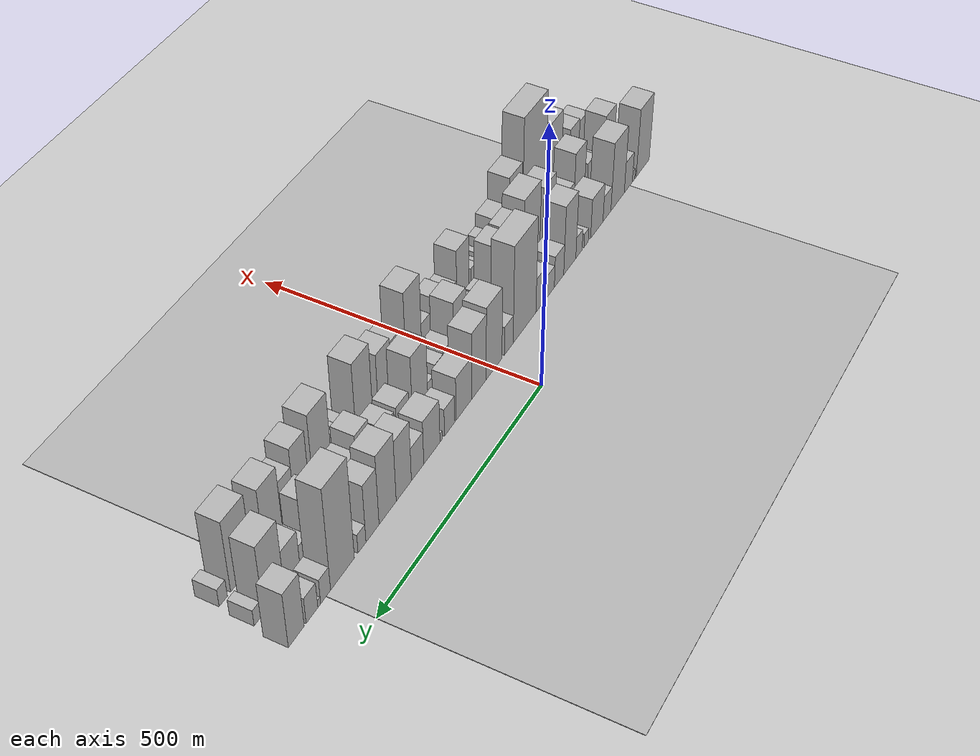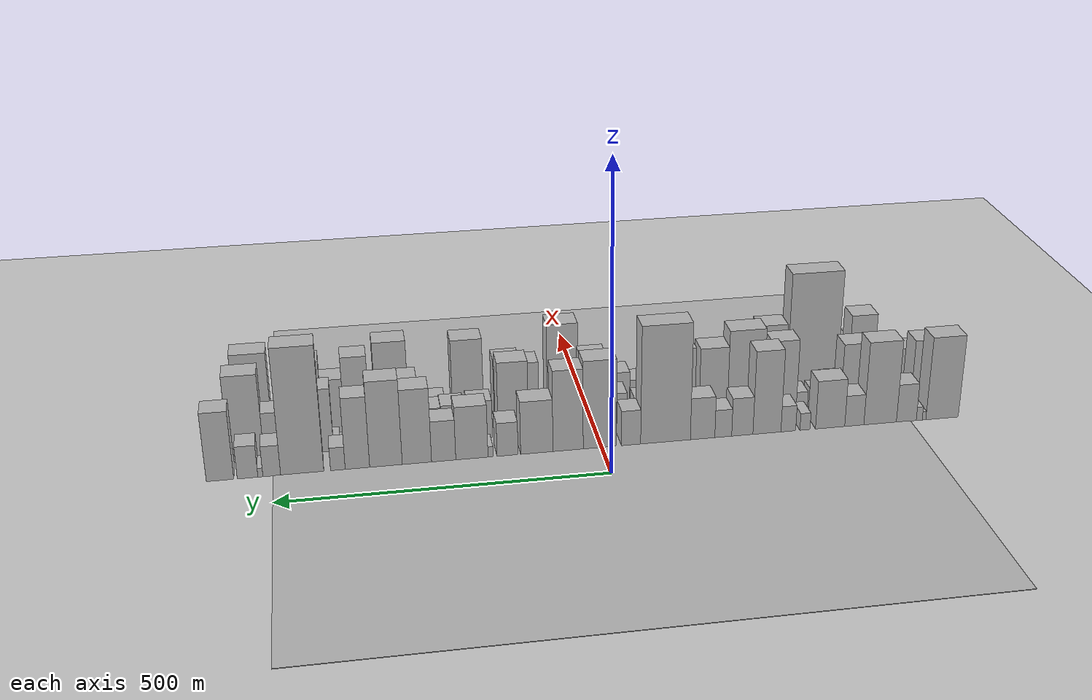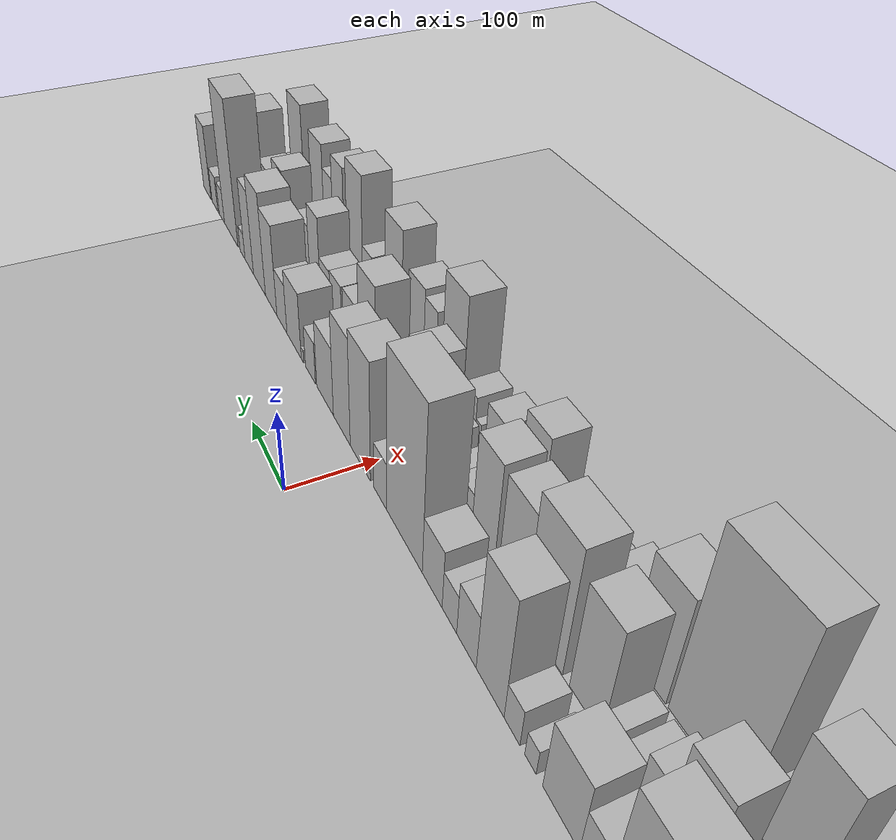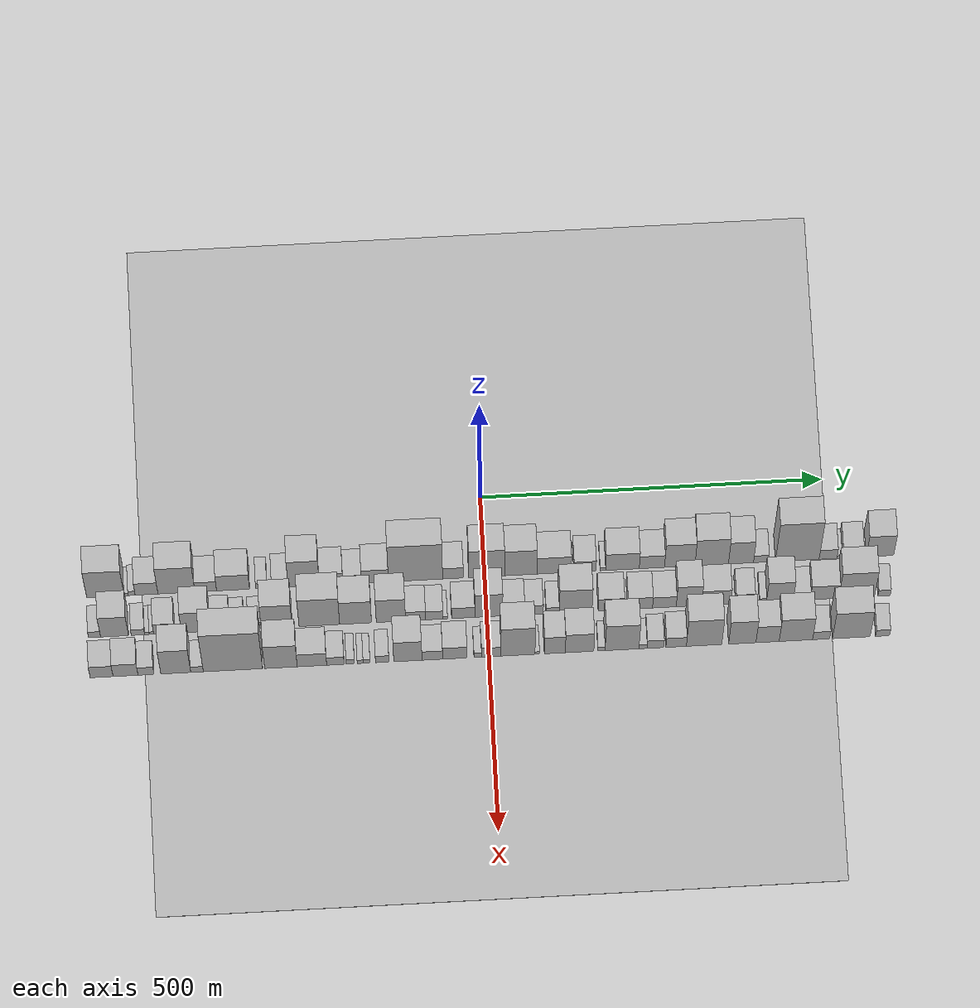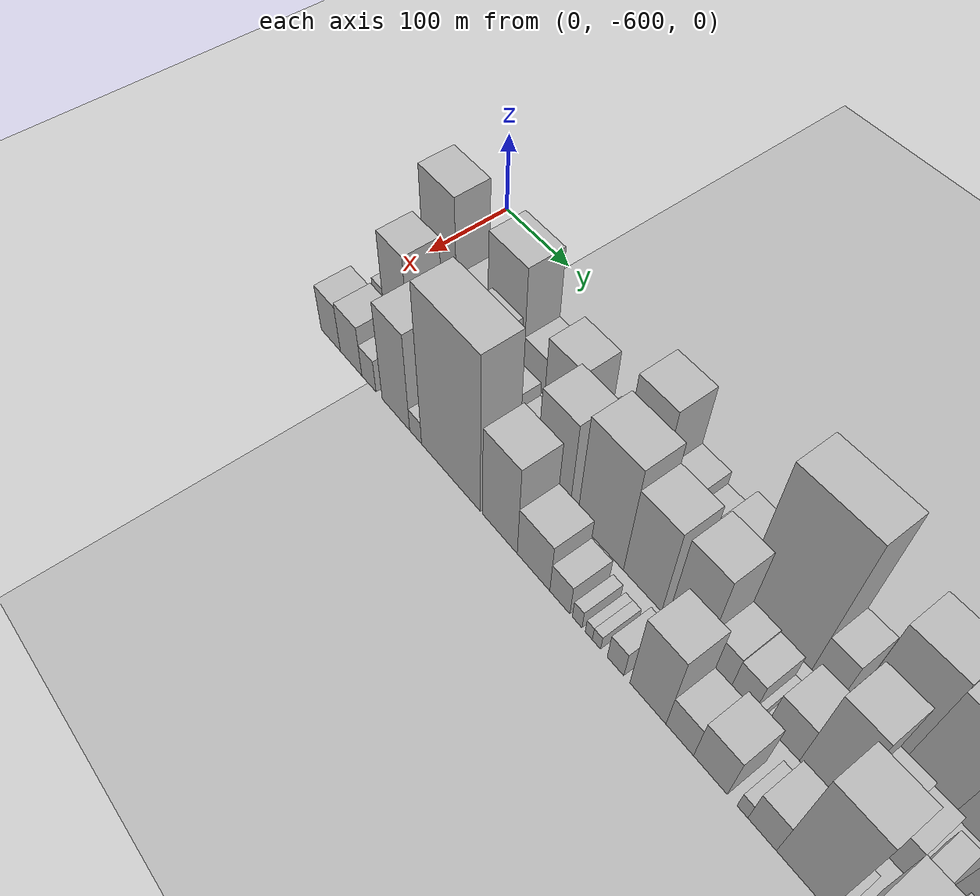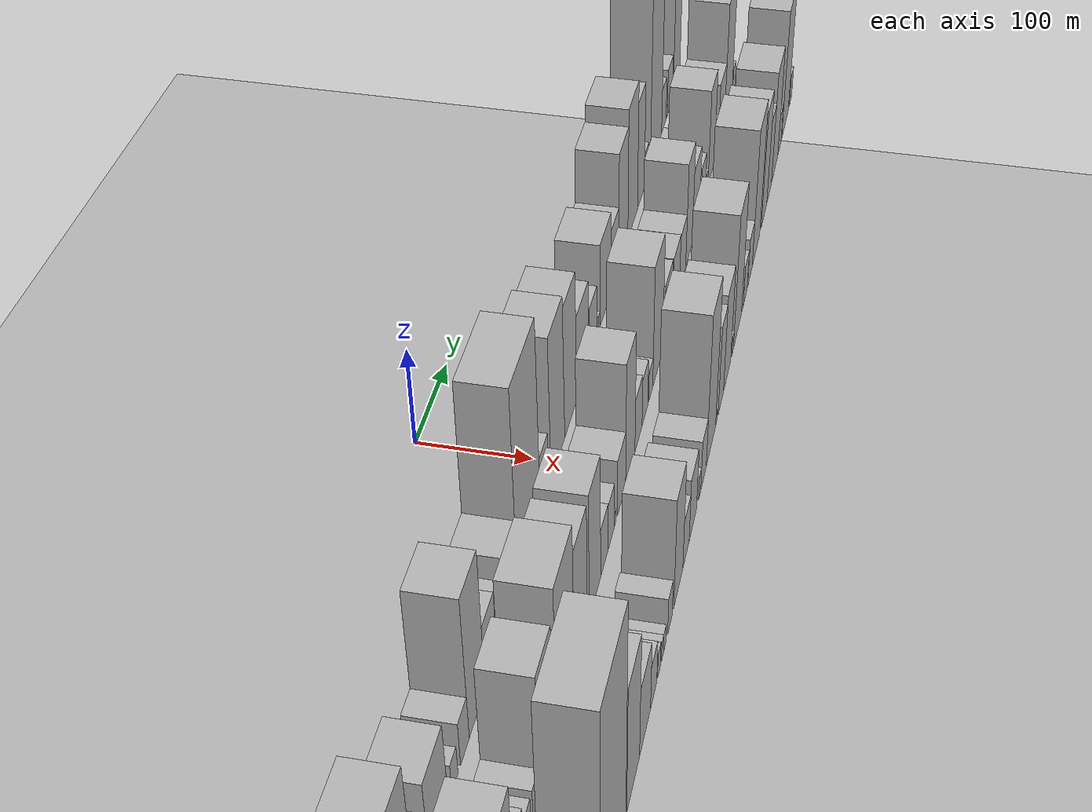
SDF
<?xml version="1.0" encoding="utf-8"?>

<sdf version="1.6">

   <world name="default">

      <gui fullscreen="0">

         <camera name="user_camera">

            <pose>-15 0 4.57585 0 0 0</pose>

            <view_controller>orbit</view_controller>

         </camera>

      </gui>

      <scene>

         <sky>

           <clouds>

             <speed>12</speed>

           </clouds>

         </sky>

         <ambient>0.4 0.4 0.4 1</ambient>

         <background>0.7 0.7 0.7 1</background>

         <shadows>1</shadows>

      </scene>

      <gravity>0 0 -9.8066</gravity>

      <magnetic_field>6e-06 2.3e-05 -4.2e-05</magnetic_field>

      <physics default="0" name="default_physics" type="ode">

         <ode>

            <solver>

               <type>quick</type>

               <iters>10</iters>

               <sor>1.0</sor>

               <use_dynamic_moi_rescaling>0</use_dynamic_moi_rescaling>

            </solver>

            <constraints>

               <cfm>0</cfm>

               <erp>0.2</erp>

               <contact_max_correcting_vel>100</contact_max_correcting_vel>

               <contact_surface_layer>0.001</contact_surface_layer>

            </constraints>

         </ode>

         <max_step_size>0.004</max_step_size>

         <real_time_factor>1</real_time_factor>

         <real_time_update_rate>250</real_time_update_rate>

      </physics>

      <light name="sun" type="directional">

         <cast_shadows>1</cast_shadows>

         <pose>0 0 10 0 0 0</pose>

         <diffuse>0.8 0.8 0.8 1</diffuse>

         <specular>0.2 0.2 0.2 1</specular>

         <attenuation>

            <range>1000</range>

            <constant>0.9</constant>

            <linear>0.01</linear>

            <quadratic>0.001</quadratic>

         </attenuation>

         <direction>-0.5 0.1 -0.9</direction>

      </light>

      <include>

         <name>ground_plane_1</name>

         <uri>model://HANNAS_ground_plane</uri>

         <pose>0 0 0  0 0 0</pose>

      </include>

      <include>

         <name>ground_plane_2</name>

         <uri>model://HANNAS_ground_plane</uri>

         <pose>100 0 0  0 0 0</pose>

      </include>

      <model name="building_1">

         <static>1</static>

         <pose frame="">100.0000 -552.7777 0 0.000000 0.000000 0.000000</pose>

         <link name="link">

            <pose frame="">0 0 72.00 0 0 0</pose>

            <collision name="collision">

               <geometry>

                  <box>

                     <size>40.0000 54.4447 144.0000</size>

                  </box>

               </geometry>

               <max_contacts>10</max_contacts>

               <surface>

                  <contact>

                     <ode/>

                  </contact>

                  <bounce/>

                  <friction>

                     <torsional>

                        <ode/>

                     </torsional>

                     <ode/>

                  </friction>

               </surface>

            </collision>

            <visual name="visual">

               <cast_shadows>0</cast_shadows>

               <geometry>

                  <box>

                     <size>40.0000 54.4447 144.0000</size>

                  </box>

               </geometry>

               <material>

                  <script>

                     <uri>model://HANNAS_wall/materials/scripts</uri>

                     <uri>model://HANNAS_wall/materials/textures</uri>

                     <name>vrc/HANNAS_wall</name>

                  </script>

               </material>

            </visual>

            <self_collide>0</self_collide>

            <enable_wind>0</enable_wind>

            <kinematic>0</kinematic>

         </link>

      </model>

      <model name="building_2">

         <static>1</static>

         <pose frame="">100.0000 -522.5342 0 0.000000 0.000000 0.000000</pose>

         <link name="link">

            <pose frame="">0 0 7.50 0 0 0</pose>

            <collision name="collision">

               <geometry>

                  <box>

                     <size>40.0000 6.0421 15.0000</size>

                  </box>

               </geometry>

               <max_contacts>10</max_contacts>

               <surface>

                  <contact>

                     <ode/>

                  </contact>

                  <bounce/>

                  <friction>

                     <torsional>

                        <ode/>

                     </torsional>

                     <ode/>

                  </friction>

               </surface>

            </collision>

            <visual name="visual">

               <cast_shadows>0</cast_shadows>

               <geometry>

                  <box>

                     <size>40.0000 6.0421 15.0000</size>

                  </box>

               </geometry>

               <material>

                  <script>

                     <uri>model://HANNAS_wall/materials/scripts</uri>

                     <uri>model://HANNAS_wall/materials/textures</uri>

                     <name>vrc/HANNAS_wall</name>

                  </script>

               </material>

            </visual>

            <self_collide>0</self_collide>

            <enable_wind>0</enable_wind>

            <kinematic>0</kinematic>

         </link>

      </model>

      <model name="building_3">

         <static>1</static>

         <pose frame="">100.0000 -514.5282 0 0.000000 0.000000 0.000000</pose>

         <link name="link">

            <pose frame="">0 0 12.00 0 0 0</pose>

            <collision name="collision">

               <geometry>

                  <box>

                     <size>40.0000 9.9699 24.0000</size>

                  </box>

               </geometry>

               <max_contacts>10</max_contacts>

               <surface>

                  <contact>

                     <ode/>

                  </contact>

                  <bounce/>

                  <friction>

                     <torsional>

                        <ode/>

                     </torsional>

                     <ode/>

                  </friction>

               </surface>

            </collision>

            <visual name="visual">

               <cast_shadows>0</cast_shadows>

               <geometry>

                  <box>

                     <size>40.0000 9.9699 24.0000</size>

                  </box>

               </geometry>

               <material>

                  <script>

                     <uri>model://HANNAS_wall/materials/scripts</uri>

                     <uri>model://HANNAS_wall/materials/textures</uri>

                     <name>vrc/HANNAS_wall</name>

                  </script>

               </material>

            </visual>

            <self_collide>0</self_collide>

            <enable_wind>0</enable_wind>

            <kinematic>0</kinematic>

         </link>

      </model>

      <model name="building_4">

         <static>1</static>

         <pose frame="">100.0000 -492.9412 0 0.000000 0.000000 0.000000</pose>

         <link name="link">

            <pose frame="">0 0 33.00 0 0 0</pose>

            <collision name="collision">

               <geometry>

                  <box>

                     <size>40.0000 33.2043 66.0000</size>

                  </box>

               </geometry>

               <max_contacts>10</max_contacts>

               <surface>

                  <contact>

                     <ode/>

                  </contact>

                  <bounce/>

                  <friction>

                     <torsional>

                        <ode/>

                     </torsional>

                     <ode/>

                  </friction>

               </surface>

            </collision>

            <visual name="visual">

               <cast_shadows>0</cast_shadows>

               <geometry>

                  <box>

                     <size>40.0000 33.2043 66.0000</size>

                  </box>

               </geometry>

               <material>

                  <script>

                     <uri>model://HANNAS_wall/materials/scripts</uri>

                     <uri>model://HANNAS_wall/materials/textures</uri>

                     <name>vrc/HANNAS_wall</name>

                  </script>

               </material>

            </visual>

            <self_collide>0</self_collide>

            <enable_wind>0</enable_wind>

            <kinematic>0</kinematic>

         </link>

      </model>

      <model name="building_5">

         <static>1</static>

         <pose frame="">100.0000 -449.3340 0 0.000000 0.000000 0.000000</pose>

         <link name="link">

            <pose frame="">0 0 72.00 0 0 0</pose>

            <collision name="collision">

               <geometry>

                  <box>

                     <size>40.0000 54.0100 144.0000</size>

                  </box>

               </geometry>

               <max_contacts>10</max_contacts>

               <surface>

                  <contact>

                     <ode/>

                  </contact>

                  <bounce/>

                  <friction>

                     <torsional>

                        <ode/>

                     </torsional>

                     <ode/>

                  </friction>

               </surface>

            </collision>

            <visual name="visual">

               <cast_shadows>0</cast_shadows>

               <geometry>

                  <box>

                     <size>40.0000 54.0100 144.0000</size>

                  </box>

               </geometry>

               <material>

                  <script>

                     <uri>model://HANNAS_wall/materials/scripts</uri>

                     <uri>model://HANNAS_wall/materials/textures</uri>

                     <name>vrc/HANNAS_wall</name>

                  </script>

               </material>

            </visual>

            <self_collide>0</self_collide>

            <enable_wind>0</enable_wind>

            <kinematic>0</kinematic>

         </link>

      </model>

      <model name="building_6">

         <static>1</static>

         <pose frame="">100.0000 -406.5440 0 0.000000 0.000000 0.000000</pose>

         <link name="link">

            <pose frame="">0 0 27.00 0 0 0</pose>

            <collision name="collision">

               <geometry>

                  <box>

                     <size>40.0000 31.5700 54.0000</size>

                  </box>

               </geometry>

               <max_contacts>10</max_contacts>

               <surface>

                  <contact>

                     <ode/>

                  </contact>

                  <bounce/>

                  <friction>

                     <torsional>

                        <ode/>

                     </torsional>

                     <ode/>

                  </friction>

               </surface>

            </collision>

            <visual name="visual">

               <cast_shadows>0</cast_shadows>

               <geometry>

                  <box>

                     <size>40.0000 31.5700 54.0000</size>

                  </box>

               </geometry>

               <material>

                  <script>

                     <uri>model://HANNAS_wall/materials/scripts</uri>

                     <uri>model://HANNAS_wall/materials/textures</uri>

                     <name>vrc/HANNAS_wall</name>

                  </script>

               </material>

            </visual>

            <self_collide>0</self_collide>

            <enable_wind>0</enable_wind>

            <kinematic>0</kinematic>

         </link>

      </model>

      <model name="building_7">

         <static>1</static>

         <pose frame="">100.0000 -366.7398 0 0.000000 0.000000 0.000000</pose>

         <link name="link">

            <pose frame="">0 0 42.00 0 0 0</pose>

            <collision name="collision">

               <geometry>

                  <box>

                     <size>40.0000 48.0384 84.0000</size>

                  </box>

               </geometry>

               <max_contacts>10</max_contacts>

               <surface>

                  <contact>

                     <ode/>

                  </contact>

                  <bounce/>

                  <friction>

                     <torsional>

                        <ode/>

                     </torsional>

                     <ode/>

                  </friction>

               </surface>

            </collision>

            <visual name="visual">

               <cast_shadows>0</cast_shadows>

               <geometry>

                  <box>

                     <size>40.0000 48.0384 84.0000</size>

                  </box>

               </geometry>

               <material>

                  <script>

                     <uri>model://HANNAS_wall/materials/scripts</uri>

                     <uri>model://HANNAS_wall/materials/textures</uri>

                     <name>vrc/HANNAS_wall</name>

                  </script>

               </material>

            </visual>

            <self_collide>0</self_collide>

            <enable_wind>0</enable_wind>

            <kinematic>0</kinematic>

         </link>

      </model>

      <model name="building_8">

         <static>1</static>

         <pose frame="">100.0000 -325.4975 0 0.000000 0.000000 0.000000</pose>

         <link name="link">

            <pose frame="">0 0 15.00 0 0 0</pose>

            <collision name="collision">

               <geometry>

                  <box>

                     <size>40.0000 16.4462 30.0000</size>

                  </box>

               </geometry>

               <max_contacts>10</max_contacts>

               <surface>

                  <contact>

                     <ode/>

                  </contact>

                  <bounce/>

                  <friction>

                     <torsional>

                        <ode/>

                     </torsional>

                     <ode/>

                  </friction>

               </surface>

            </collision>

            <visual name="visual">

               <cast_shadows>0</cast_shadows>

               <geometry>

                  <box>

                     <size>40.0000 16.4462 30.0000</size>

                  </box>

               </geometry>

               <material>

                  <script>

                     <uri>model://HANNAS_wall/materials/scripts</uri>

                     <uri>model://HANNAS_wall/materials/textures</uri>

                     <name>vrc/HANNAS_wall</name>

                  </script>

               </material>

            </visual>

            <self_collide>0</self_collide>

            <enable_wind>0</enable_wind>

            <kinematic>0</kinematic>

         </link>

      </model>

      <model name="building_9">

         <static>1</static>

         <pose frame="">100.0000 -298.2725 0 0.000000 0.000000 0.000000</pose>

         <link name="link">

            <pose frame="">0 0 22.50 0 0 0</pose>

            <collision name="collision">

               <geometry>

                  <box>

                     <size>40.0000 24.0039 45.0000</size>

                  </box>

               </geometry>

               <max_contacts>10</max_contacts>

               <surface>

                  <contact>

                     <ode/>

                  </contact>

                  <bounce/>

                  <friction>

                     <torsional>

                        <ode/>

                     </torsional>

                     <ode/>

                  </friction>

               </surface>

            </collision>

            <visual name="visual">

               <cast_shadows>0</cast_shadows>

               <geometry>

                  <box>

                     <size>40.0000 24.0039 45.0000</size>

                  </box>

               </geometry>

               <material>

                  <script>

                     <uri>model://HANNAS_wall/materials/scripts</uri>

                     <uri>model://HANNAS_wall/materials/textures</uri>

                     <name>vrc/HANNAS_wall</name>

                  </script>

               </material>

            </visual>

            <self_collide>0</self_collide>

            <enable_wind>0</enable_wind>

            <kinematic>0</kinematic>

         </link>

      </model>

      <model name="building_10">

         <static>1</static>

         <pose frame="">100.0000 -263.5627 0 0.000000 0.000000 0.000000</pose>

         <link name="link">

            <pose frame="">0 0 72.00 0 0 0</pose>

            <collision name="collision">

               <geometry>

                  <box>

                     <size>40.0000 45.4156 144.0000</size>

                  </box>

               </geometry>

               <max_contacts>10</max_contacts>

               <surface>

                  <contact>

                     <ode/>

                  </contact>

                  <bounce/>

                  <friction>

                     <torsional>

                        <ode/>

                     </torsional>

                     <ode/>

                  </friction>

               </surface>

            </collision>

            <visual name="visual">

               <cast_shadows>0</cast_shadows>

               <geometry>

                  <box>

                     <size>40.0000 45.4156 144.0000</size>

                  </box>

               </geometry>

               <material>

                  <script>

                     <uri>model://HANNAS_wall/materials/scripts</uri>

                     <uri>model://HANNAS_wall/materials/textures</uri>

                     <name>vrc/HANNAS_wall</name>

                  </script>

               </material>

            </visual>

            <self_collide>0</self_collide>

            <enable_wind>0</enable_wind>

            <kinematic>0</kinematic>

         </link>

      </model>

      <model name="building_11">

         <static>1</static>

         <pose frame="">100.0000 -223.7053 0 0.000000 0.000000 0.000000</pose>

         <link name="link">

            <pose frame="">0 0 33.00 0 0 0</pose>

            <collision name="collision">

               <geometry>

                  <box>

                     <size>40.0000 34.2993 66.0000</size>

                  </box>

               </geometry>

               <max_contacts>10</max_contacts>

               <surface>

                  <contact>

                     <ode/>

                  </contact>

                  <bounce/>

                  <friction>

                     <torsional>

                        <ode/>

                     </torsional>

                     <ode/>

                  </friction>

               </surface>

            </collision>

            <visual name="visual">

               <cast_shadows>0</cast_shadows>

               <geometry>

                  <box>

                     <size>40.0000 34.2993 66.0000</size>

                  </box>

               </geometry>

               <material>

                  <script>

                     <uri>model://HANNAS_wall/materials/scripts</uri>

                     <uri>model://HANNAS_wall/materials/textures</uri>

                     <name>vrc/HANNAS_wall</name>

                  </script>

               </material>

            </visual>

            <self_collide>0</self_collide>

            <enable_wind>0</enable_wind>

            <kinematic>0</kinematic>

         </link>

      </model>

      <model name="building_12">

         <static>1</static>

         <pose frame="">100.0000 -193.0056 0 0.000000 0.000000 0.000000</pose>

         <link name="link">

            <pose frame="">0 0 24.00 0 0 0</pose>

            <collision name="collision">

               <geometry>

                  <box>

                     <size>40.0000 27.1000 48.0000</size>

                  </box>

               </geometry>

               <max_contacts>10</max_contacts>

               <surface>

                  <contact>

                     <ode/>

                  </contact>

                  <bounce/>

                  <friction>

                     <torsional>

                        <ode/>

                     </torsional>

                     <ode/>

                  </friction>

               </surface>

            </collision>

            <visual name="visual">

               <cast_shadows>0</cast_shadows>

               <geometry>

                  <box>

                     <size>40.0000 27.1000 48.0000</size>

                  </box>

               </geometry>

               <material>

                  <script>

                     <uri>model://HANNAS_wall/materials/scripts</uri>

                     <uri>model://HANNAS_wall/materials/textures</uri>

                     <name>vrc/HANNAS_wall</name>

                  </script>

               </material>

            </visual>

            <self_collide>0</self_collide>

            <enable_wind>0</enable_wind>

            <kinematic>0</kinematic>

         </link>

      </model>

      <model name="building_13">

         <static>1</static>

         <pose frame="">100.0000 -159.8613 0 0.000000 0.000000 0.000000</pose>

         <link name="link">

            <pose frame="">0 0 36.00 0 0 0</pose>

            <collision name="collision">

               <geometry>

                  <box>

                     <size>40.0000 39.1886 72.0000</size>

                  </box>

               </geometry>

               <max_contacts>10</max_contacts>

               <surface>

                  <contact>

                     <ode/>

                  </contact>

                  <bounce/>

                  <friction>

                     <torsional>

                        <ode/>

                     </torsional>

                     <ode/>

                  </friction>

               </surface>

            </collision>

            <visual name="visual">

               <cast_shadows>0</cast_shadows>

               <geometry>

                  <box>

                     <size>40.0000 39.1886 72.0000</size>

                  </box>

               </geometry>

               <material>

                  <script>

                     <uri>model://HANNAS_wall/materials/scripts</uri>

                     <uri>model://HANNAS_wall/materials/textures</uri>

                     <name>vrc/HANNAS_wall</name>

                  </script>

               </material>

            </visual>

            <self_collide>0</self_collide>

            <enable_wind>0</enable_wind>

            <kinematic>0</kinematic>

         </link>

      </model>

      <model name="building_14">

         <static>1</static>

         <pose frame="">100.0000 -100.7427 0 0.000000 0.000000 0.000000</pose>

         <link name="link">

            <pose frame="">0 0 100.50 0 0 0</pose>

            <collision name="collision">

               <geometry>

                  <box>

                     <size>40.0000 79.0486 201.0000</size>

                  </box>

               </geometry>

               <max_contacts>10</max_contacts>

               <surface>

                  <contact>

                     <ode/>

                  </contact>

                  <bounce/>

                  <friction>

                     <torsional>

                        <ode/>

                     </torsional>

                     <ode/>

                  </friction>

               </surface>

            </collision>

            <visual name="visual">

               <cast_shadows>0</cast_shadows>

               <geometry>

                  <box>

                     <size>40.0000 79.0486 201.0000</size>

                  </box>

               </geometry>

               <material>

                  <script>

                     <uri>model://HANNAS_wall/materials/scripts</uri>

                     <uri>model://HANNAS_wall/materials/textures</uri>

                     <name>vrc/HANNAS_wall</name>

                  </script>

               </material>

            </visual>

            <self_collide>0</self_collide>

            <enable_wind>0</enable_wind>

            <kinematic>0</kinematic>

         </link>

      </model>

      <model name="building_15">

         <static>1</static>

         <pose frame="">100.0000 -46.0944 0 0.000000 0.000000 0.000000</pose>

         <link name="link">

            <pose frame="">0 0 30.00 0 0 0</pose>

            <collision name="collision">

               <geometry>

                  <box>

                     <size>40.0000 30.2478 60.0000</size>

                  </box>

               </geometry>

               <max_contacts>10</max_contacts>

               <surface>

                  <contact>

                     <ode/>

                  </contact>

                  <bounce/>

                  <friction>

                     <torsional>

                        <ode/>

                     </torsional>

                     <ode/>

                  </friction>

               </surface>

            </collision>

            <visual name="visual">

               <cast_shadows>0</cast_shadows>

               <geometry>

                  <box>

                     <size>40.0000 30.2478 60.0000</size>

                  </box>

               </geometry>

               <material>

                  <script>

                     <uri>model://HANNAS_wall/materials/scripts</uri>

                     <uri>model://HANNAS_wall/materials/textures</uri>

                     <name>vrc/HANNAS_wall</name>

                  </script>

               </material>

            </visual>

            <self_collide>0</self_collide>

            <enable_wind>0</enable_wind>

            <kinematic>0</kinematic>

         </link>

      </model>

      <model name="building_16">

         <static>1</static>

         <pose frame="">100.0000 3.0537 0 0.000000 0.000000 0.000000</pose>

         <link name="link">

            <pose frame="">0 0 75.00 0 0 0</pose>

            <collision name="collision">

               <geometry>

                  <box>

                     <size>40.0000 52.0484 150.0000</size>

                  </box>

               </geometry>

               <max_contacts>10</max_contacts>

               <surface>

                  <contact>

                     <ode/>

                  </contact>

                  <bounce/>

                  <friction>

                     <torsional>

                        <ode/>

                     </torsional>

                     <ode/>

                  </friction>

               </surface>

            </collision>

            <visual name="visual">

               <cast_shadows>0</cast_shadows>

               <geometry>

                  <box>

                     <size>40.0000 52.0484 150.0000</size>

                  </box>

               </geometry>

               <material>

                  <script>

                     <uri>model://HANNAS_wall/materials/scripts</uri>

                     <uri>model://HANNAS_wall/materials/textures</uri>

                     <name>vrc/HANNAS_wall</name>

                  </script>

               </material>

            </visual>

            <self_collide>0</self_collide>

            <enable_wind>0</enable_wind>

            <kinematic>0</kinematic>

         </link>

      </model>

      <model name="building_17">

         <static>1</static>

         <pose frame="">100.0000 52.6405 0 0.000000 0.000000 0.000000</pose>

         <link name="link">

            <pose frame="">0 0 69.00 0 0 0</pose>

            <collision name="collision">

               <geometry>

                  <box>

                     <size>40.0000 47.1252 138.0000</size>

                  </box>

               </geometry>

               <max_contacts>10</max_contacts>

               <surface>

                  <contact>

                     <ode/>

                  </contact>

                  <bounce/>

                  <friction>

                     <torsional>

                        <ode/>

                     </torsional>

                     <ode/>

                  </friction>

               </surface>

            </collision>

            <visual name="visual">

               <cast_shadows>0</cast_shadows>

               <geometry>

                  <box>

                     <size>40.0000 47.1252 138.0000</size>

                  </box>

               </geometry>

               <material>

                  <script>

                     <uri>model://HANNAS_wall/materials/scripts</uri>

                     <uri>model://HANNAS_wall/materials/textures</uri>

                     <name>vrc/HANNAS_wall</name>

                  </script>

               </material>

            </visual>

            <self_collide>0</self_collide>

            <enable_wind>0</enable_wind>

            <kinematic>0</kinematic>

         </link>

      </model>

      <model name="building_18">

         <static>1</static>

         <pose frame="">100.0000 101.2322 0 0.000000 0.000000 0.000000</pose>

         <link name="link">

            <pose frame="">0 0 45.00 0 0 0</pose>

            <collision name="collision">

               <geometry>

                  <box>

                     <size>40.0000 50.0583 90.0000</size>

                  </box>

               </geometry>

               <max_contacts>10</max_contacts>

               <surface>

                  <contact>

                     <ode/>

                  </contact>

                  <bounce/>

                  <friction>

                     <torsional>

                        <ode/>

                     </torsional>

                     <ode/>

                  </friction>

               </surface>

            </collision>

            <visual name="visual">

               <cast_shadows>0</cast_shadows>

               <geometry>

                  <box>

                     <size>40.0000 50.0583 90.0000</size>

                  </box>

               </geometry>

               <material>

                  <script>

                     <uri>model://HANNAS_wall/materials/scripts</uri>

                     <uri>model://HANNAS_wall/materials/textures</uri>

                     <name>vrc/HANNAS_wall</name>

                  </script>

               </material>

            </visual>

            <self_collide>0</self_collide>

            <enable_wind>0</enable_wind>

            <kinematic>0</kinematic>

         </link>

      </model>

      <model name="building_19">

         <static>1</static>

         <pose frame="">100.0000 146.4236 0 0.000000 0.000000 0.000000</pose>

         <link name="link">

            <pose frame="">0 0 28.50 0 0 0</pose>

            <collision name="collision">

               <geometry>

                  <box>

                     <size>40.0000 32.3245 57.0000</size>

                  </box>

               </geometry>

               <max_contacts>10</max_contacts>

               <surface>

                  <contact>

                     <ode/>

                  </contact>

                  <bounce/>

                  <friction>

                     <torsional>

                        <ode/>

                     </torsional>

                     <ode/>

                  </friction>

               </surface>

            </collision>

            <visual name="visual">

               <cast_shadows>0</cast_shadows>

               <geometry>

                  <box>

                     <size>40.0000 32.3245 57.0000</size>

                  </box>

               </geometry>

               <material>

                  <script>

                     <uri>model://HANNAS_wall/materials/scripts</uri>

                     <uri>model://HANNAS_wall/materials/textures</uri>

                     <name>vrc/HANNAS_wall</name>

                  </script>

               </material>

            </visual>

            <self_collide>0</self_collide>

            <enable_wind>0</enable_wind>

            <kinematic>0</kinematic>

         </link>

      </model>

      <model name="building_20">

         <static>1</static>

         <pose frame="">100.0000 172.5480 0 0.000000 0.000000 0.000000</pose>

         <link name="link">

            <pose frame="">0 0 9.00 0 0 0</pose>

            <collision name="collision">

               <geometry>

                  <box>

                     <size>40.0000 7.9243 18.0000</size>

                  </box>

               </geometry>

               <max_contacts>10</max_contacts>

               <surface>

                  <contact>

                     <ode/>

                  </contact>

                  <bounce/>

                  <friction>

                     <torsional>

                        <ode/>

                     </torsional>

                     <ode/>

                  </friction>

               </surface>

            </collision>

            <visual name="visual">

               <cast_shadows>0</cast_shadows>

               <geometry>

                  <box>

                     <size>40.0000 7.9243 18.0000</size>

                  </box>

               </geometry>

               <material>

                  <script>

                     <uri>model://HANNAS_wall/materials/scripts</uri>

                     <uri>model://HANNAS_wall/materials/textures</uri>

                     <name>vrc/HANNAS_wall</name>

                  </script>

               </material>

            </visual>

            <self_collide>0</self_collide>

            <enable_wind>0</enable_wind>

            <kinematic>0</kinematic>

         </link>

      </model>

      <model name="building_21">

         <static>1</static>

         <pose frame="">100.0000 201.1346 0 0.000000 0.000000 0.000000</pose>

         <link name="link">

            <pose frame="">0 0 45.00 0 0 0</pose>

            <collision name="collision">

               <geometry>

                  <box>

                     <size>40.0000 49.2489 90.0000</size>

                  </box>

               </geometry>

               <max_contacts>10</max_contacts>

               <surface>

                  <contact>

                     <ode/>

                  </contact>

                  <bounce/>

                  <friction>

                     <torsional>

                        <ode/>

                     </torsional>

                     <ode/>

                  </friction>

               </surface>

            </collision>

            <visual name="visual">

               <cast_shadows>0</cast_shadows>

               <geometry>

                  <box>

                     <size>40.0000 49.2489 90.0000</size>

                  </box>

               </geometry>

               <material>

                  <script>

                     <uri>model://HANNAS_wall/materials/scripts</uri>

                     <uri>model://HANNAS_wall/materials/textures</uri>

                     <name>vrc/HANNAS_wall</name>

                  </script>

               </material>

            </visual>

            <self_collide>0</self_collide>

            <enable_wind>0</enable_wind>

            <kinematic>0</kinematic>

         </link>

      </model>

      <model name="building_22">

         <static>1</static>

         <pose frame="">100.0000 244.1999 0 0.000000 0.000000 0.000000</pose>

         <link name="link">

            <pose frame="">0 0 34.50 0 0 0</pose>

            <collision name="collision">

               <geometry>

                  <box>

                     <size>40.0000 36.8816 69.0000</size>

                  </box>

               </geometry>

               <max_contacts>10</max_contacts>

               <surface>

                  <contact>

                     <ode/>

                  </contact>

                  <bounce/>

                  <friction>

                     <torsional>

                        <ode/>

                     </torsional>

                     <ode/>

                  </friction>

               </surface>

            </collision>

            <visual name="visual">

               <cast_shadows>0</cast_shadows>

               <geometry>

                  <box>

                     <size>40.0000 36.8816 69.0000</size>

                  </box>

               </geometry>

               <material>

                  <script>

                     <uri>model://HANNAS_wall/materials/scripts</uri>

                     <uri>model://HANNAS_wall/materials/textures</uri>

                     <name>vrc/HANNAS_wall</name>

                  </script>

               </material>

            </visual>

            <self_collide>0</self_collide>

            <enable_wind>0</enable_wind>

            <kinematic>0</kinematic>

         </link>

      </model>

      <model name="building_23">

         <static>1</static>

         <pose frame="">100.0000 284.8170 0 0.000000 0.000000 0.000000</pose>

         <link name="link">

            <pose frame="">0 0 63.00 0 0 0</pose>

            <collision name="collision">

               <geometry>

                  <box>

                     <size>40.0000 44.3525 126.0000</size>

                  </box>

               </geometry>

               <max_contacts>10</max_contacts>

               <surface>

                  <contact>

                     <ode/>

                  </contact>

                  <bounce/>

                  <friction>

                     <torsional>

                        <ode/>

                     </torsional>

                     <ode/>

                  </friction>

               </surface>

            </collision>

            <visual name="visual">

               <cast_shadows>0</cast_shadows>

               <geometry>

                  <box>

                     <size>40.0000 44.3525 126.0000</size>

                  </box>

               </geometry>

               <material>

                  <script>

                     <uri>model://HANNAS_wall/materials/scripts</uri>

                     <uri>model://HANNAS_wall/materials/textures</uri>

                     <name>vrc/HANNAS_wall</name>

                  </script>

               </material>

            </visual>

            <self_collide>0</self_collide>

            <enable_wind>0</enable_wind>

            <kinematic>0</kinematic>

         </link>

      </model>

      <model name="building_24">

         <static>1</static>

         <pose frame="">100.0000 331.4982 0 0.000000 0.000000 0.000000</pose>

         <link name="link">

            <pose frame="">0 0 72.00 0 0 0</pose>

            <collision name="collision">

               <geometry>

                  <box>

                     <size>40.0000 49.0100 144.0000</size>

                  </box>

               </geometry>

               <max_contacts>10</max_contacts>

               <surface>

                  <contact>

                     <ode/>

                  </contact>

                  <bounce/>

                  <friction>

                     <torsional>

                        <ode/>

                     </torsional>

                     <ode/>

                  </friction>

               </surface>

            </collision>

            <visual name="visual">

               <cast_shadows>0</cast_shadows>

               <geometry>

                  <box>

                     <size>40.0000 49.0100 144.0000</size>

                  </box>

               </geometry>

               <material>

                  <script>

                     <uri>model://HANNAS_wall/materials/scripts</uri>

                     <uri>model://HANNAS_wall/materials/textures</uri>

                     <name>vrc/HANNAS_wall</name>

                  </script>

               </material>

            </visual>

            <self_collide>0</self_collide>

            <enable_wind>0</enable_wind>

            <kinematic>0</kinematic>

         </link>

      </model>

      <model name="building_25">

         <static>1</static>

         <pose frame="">100.0000 374.3059 0 0.000000 0.000000 0.000000</pose>

         <link name="link">

            <pose frame="">0 0 60.00 0 0 0</pose>

            <collision name="collision">

               <geometry>

                  <box>

                     <size>40.0000 36.6054 120.0000</size>

                  </box>

               </geometry>

               <max_contacts>10</max_contacts>

               <surface>

                  <contact>

                     <ode/>

                  </contact>

                  <bounce/>

                  <friction>

                     <torsional>

                        <ode/>

                     </torsional>

                     <ode/>

                  </friction>

               </surface>

            </collision>

            <visual name="visual">

               <cast_shadows>0</cast_shadows>

               <geometry>

                  <box>

                     <size>40.0000 36.6054 120.0000</size>

                  </box>

               </geometry>

               <material>

                  <script>

                     <uri>model://HANNAS_wall/materials/scripts</uri>

                     <uri>model://HANNAS_wall/materials/textures</uri>

                     <name>vrc/HANNAS_wall</name>

                  </script>

               </material>

            </visual>

            <self_collide>0</self_collide>

            <enable_wind>0</enable_wind>

            <kinematic>0</kinematic>

         </link>

      </model>

      <model name="building_26">

         <static>1</static>

         <pose frame="">100.0000 403.5594 0 0.000000 0.000000 0.000000</pose>

         <link name="link">

            <pose frame="">0 0 19.50 0 0 0</pose>

            <collision name="collision">

               <geometry>

                  <box>

                     <size>40.0000 21.9015 39.0000</size>

                  </box>

               </geometry>

               <max_contacts>10</max_contacts>

               <surface>

                  <contact>

                     <ode/>

                  </contact>

                  <bounce/>

                  <friction>

                     <torsional>

                        <ode/>

                     </torsional>

                     <ode/>

                  </friction>

               </surface>

            </collision>

            <visual name="visual">

               <cast_shadows>0</cast_shadows>

               <geometry>

                  <box>

                     <size>40.0000 21.9015 39.0000</size>

                  </box>

               </geometry>

               <material>

                  <script>

                     <uri>model://HANNAS_wall/materials/scripts</uri>

                     <uri>model://HANNAS_wall/materials/textures</uri>

                     <name>vrc/HANNAS_wall</name>

                  </script>

               </material>

            </visual>

            <self_collide>0</self_collide>

            <enable_wind>0</enable_wind>

            <kinematic>0</kinematic>

         </link>

      </model>

      <model name="building_27">

         <static>1</static>

         <pose frame="">100.0000 456.4815 0 0.000000 0.000000 0.000000</pose>

         <link name="link">

            <pose frame="">0 0 105.00 0 0 0</pose>

            <collision name="collision">

               <geometry>

                  <box>

                     <size>40.0000 63.9427 210.0000</size>

                  </box>

               </geometry>

               <max_contacts>10</max_contacts>

               <surface>

                  <contact>

                     <ode/>

                  </contact>

                  <bounce/>

                  <friction>

                     <torsional>

                        <ode/>

                     </torsional>

                     <ode/>

                  </friction>

               </surface>

            </collision>

            <visual name="visual">

               <cast_shadows>0</cast_shadows>

               <geometry>

                  <box>

                     <size>40.0000 63.9427 210.0000</size>

                  </box>

               </geometry>

               <material>

                  <script>

                     <uri>model://HANNAS_wall/materials/scripts</uri>

                     <uri>model://HANNAS_wall/materials/textures</uri>

                     <name>vrc/HANNAS_wall</name>

                  </script>

               </material>

            </visual>

            <self_collide>0</self_collide>

            <enable_wind>0</enable_wind>

            <kinematic>0</kinematic>

         </link>

      </model>

      <model name="building_28">

         <static>1</static>

         <pose frame="">100.0000 501.5119 0 0.000000 0.000000 0.000000</pose>

         <link name="link">

            <pose frame="">0 0 25.50 0 0 0</pose>

            <collision name="collision">

               <geometry>

                  <box>

                     <size>40.0000 26.1181 51.0000</size>

                  </box>

               </geometry>

               <max_contacts>10</max_contacts>

               <surface>

                  <contact>

                     <ode/>

                  </contact>

                  <bounce/>

                  <friction>

                     <torsional>

                        <ode/>

                     </torsional>

                     <ode/>

                  </friction>

               </surface>

            </collision>

            <visual name="visual">

               <cast_shadows>0</cast_shadows>

               <geometry>

                  <box>

                     <size>40.0000 26.1181 51.0000</size>

                  </box>

               </geometry>

               <material>

                  <script>

                     <uri>model://HANNAS_wall/materials/scripts</uri>

                     <uri>model://HANNAS_wall/materials/textures</uri>

                     <name>vrc/HANNAS_wall</name>

                  </script>

               </material>

            </visual>

            <self_collide>0</self_collide>

            <enable_wind>0</enable_wind>

            <kinematic>0</kinematic>

         </link>

      </model>

      <model name="building_29">

         <static>1</static>

         <pose frame="">100.0000 518.2382 0 0.000000 0.000000 0.000000</pose>

         <link name="link">

            <pose frame="">0 0 7.50 0 0 0</pose>

            <collision name="collision">

               <geometry>

                  <box>

                     <size>40.0000 7.3345 15.0000</size>

                  </box>

               </geometry>

               <max_contacts>10</max_contacts>

               <surface>

                  <contact>

                     <ode/>

                  </contact>

                  <bounce/>

                  <friction>

                     <torsional>

                        <ode/>

                     </torsional>

                     <ode/>

                  </friction>

               </surface>

            </collision>

            <visual name="visual">

               <cast_shadows>0</cast_shadows>

               <geometry>

                  <box>

                     <size>40.0000 7.3345 15.0000</size>

                  </box>

               </geometry>

               <material>

                  <script>

                     <uri>model://HANNAS_wall/materials/scripts</uri>

                     <uri>model://HANNAS_wall/materials/textures</uri>

                     <name>vrc/HANNAS_wall</name>

                  </script>

               </material>

            </visual>

            <self_collide>0</self_collide>

            <enable_wind>0</enable_wind>

            <kinematic>0</kinematic>

         </link>

      </model>

      <model name="building_30">

         <static>1</static>

         <pose frame="">100.0000 537.0584 0 0.000000 0.000000 0.000000</pose>

         <link name="link">

            <pose frame="">0 0 27.00 0 0 0</pose>

            <collision name="collision">

               <geometry>

                  <box>

                     <size>40.0000 30.3059 54.0000</size>

                  </box>

               </geometry>

               <max_contacts>10</max_contacts>

               <surface>

                  <contact>

                     <ode/>

                  </contact>

                  <bounce/>

                  <friction>

                     <torsional>

                        <ode/>

                     </torsional>

                     <ode/>

                  </friction>

               </surface>

            </collision>

            <visual name="visual">

               <cast_shadows>0</cast_shadows>

               <geometry>

                  <box>

                     <size>40.0000 30.3059 54.0000</size>

                  </box>

               </geometry>

               <material>

                  <script>

                     <uri>model://HANNAS_wall/materials/scripts</uri>

                     <uri>model://HANNAS_wall/materials/textures</uri>

                     <name>vrc/HANNAS_wall</name>

                  </script>

               </material>

            </visual>

            <self_collide>0</self_collide>

            <enable_wind>0</enable_wind>

            <kinematic>0</kinematic>

         </link>

      </model>

      <model name="building_31">

         <static>1</static>

         <pose frame="">100.0000 577.2599 0 0.000000 0.000000 0.000000</pose>

         <link name="link">

            <pose frame="">0 0 57.00 0 0 0</pose>

            <collision name="collision">

               <geometry>

                  <box>

                     <size>40.0000 40.0972 114.0000</size>

                  </box>

               </geometry>

               <max_contacts>10</max_contacts>

               <surface>

                  <contact>

                     <ode/>

                  </contact>

                  <bounce/>

                  <friction>

                     <torsional>

                        <ode/>

                     </torsional>

                     <ode/>

                  </friction>

               </surface>

            </collision>

            <visual name="visual">

               <cast_shadows>0</cast_shadows>

               <geometry>

                  <box>

                     <size>40.0000 40.0972 114.0000</size>

                  </box>

               </geometry>

               <material>

                  <script>

                     <uri>model://HANNAS_wall/materials/scripts</uri>

                     <uri>model://HANNAS_wall/materials/textures</uri>

                     <name>vrc/HANNAS_wall</name>

                  </script>

               </material>

            </visual>

            <self_collide>0</self_collide>

            <enable_wind>0</enable_wind>

            <kinematic>0</kinematic>

         </link>

      </model>

      <model name="building_32">

         <static>1</static>

         <pose frame="">160.0000 -571.1859 0 0.000000 0.000000 0.000000</pose>

         <link name="link">

            <pose frame="">0 0 16.50 0 0 0</pose>

            <collision name="collision">

               <geometry>

                  <box>

                     <size>40.0000 17.6282 33.0000</size>

                  </box>

               </geometry>

               <max_contacts>10</max_contacts>

               <surface>

                  <contact>

                     <ode/>

                  </contact>

                  <bounce/>

                  <friction>

                     <torsional>

                        <ode/>

                     </torsional>

                     <ode/>

                  </friction>

               </surface>

            </collision>

            <visual name="visual">

               <cast_shadows>0</cast_shadows>

               <geometry>

                  <box>

                     <size>40.0000 17.6282 33.0000</size>

                  </box>

               </geometry>

               <material>

                  <script>

                     <uri>model://HANNAS_wall/materials/scripts</uri>

                     <uri>model://HANNAS_wall/materials/textures</uri>

                     <name>vrc/HANNAS_wall</name>

                  </script>

               </material>

            </visual>

            <self_collide>0</self_collide>

            <enable_wind>0</enable_wind>

            <kinematic>0</kinematic>

         </link>

      </model>

      <model name="building_33">

         <static>1</static>

         <pose frame="">160.0000 -542.0684 0 0.000000 0.000000 0.000000</pose>

         <link name="link">

            <pose frame="">0 0 55.50 0 0 0</pose>

            <collision name="collision">

               <geometry>

                  <box>

                     <size>40.0000 40.6069 111.0000</size>

                  </box>

               </geometry>

               <max_contacts>10</max_contacts>

               <surface>

                  <contact>

                     <ode/>

                  </contact>

                  <bounce/>

                  <friction>

                     <torsional>

                        <ode/>

                     </torsional>

                     <ode/>

                  </friction>

               </surface>

            </collision>

            <visual name="visual">

               <cast_shadows>0</cast_shadows>

               <geometry>

                  <box>

                     <size>40.0000 40.6069 111.0000</size>

                  </box>

               </geometry>

               <material>

                  <script>

                     <uri>model://HANNAS_wall/materials/scripts</uri>

                     <uri>model://HANNAS_wall/materials/textures</uri>

                     <name>vrc/HANNAS_wall</name>

                  </script>

               </material>

            </visual>

            <self_collide>0</self_collide>

            <enable_wind>0</enable_wind>

            <kinematic>0</kinematic>

         </link>

      </model>

      <model name="building_34">

         <static>1</static>

         <pose frame="">160.0000 -507.9775 0 0.000000 0.000000 0.000000</pose>

         <link name="link">

            <pose frame="">0 0 16.50 0 0 0</pose>

            <collision name="collision">

               <geometry>

                  <box>

                     <size>40.0000 19.5749 33.0000</size>

                  </box>

               </geometry>

               <max_contacts>10</max_contacts>

               <surface>

                  <contact>

                     <ode/>

                  </contact>

                  <bounce/>

                  <friction>

                     <torsional>

                        <ode/>

                     </torsional>

                     <ode/>

                  </friction>

               </surface>

            </collision>

            <visual name="visual">

               <cast_shadows>0</cast_shadows>

               <geometry>

                  <box>

                     <size>40.0000 19.5749 33.0000</size>

                  </box>

               </geometry>

               <material>

                  <script>

                     <uri>model://HANNAS_wall/materials/scripts</uri>

                     <uri>model://HANNAS_wall/materials/textures</uri>

                     <name>vrc/HANNAS_wall</name>

                  </script>

               </material>

            </visual>

            <self_collide>0</self_collide>

            <enable_wind>0</enable_wind>

            <kinematic>0</kinematic>

         </link>

      </model>

      <model name="building_35">

         <static>1</static>

         <pose frame="">160.0000 -494.9289 0 0.000000 0.000000 0.000000</pose>

         <link name="link">

            <pose frame="">0 0 7.50 0 0 0</pose>

            <collision name="collision">

               <geometry>

                  <box>

                     <size>40.0000 6.5223 15.0000</size>

                  </box>

               </geometry>

               <max_contacts>10</max_contacts>

               <surface>

                  <contact>

                     <ode/>

                  </contact>

                  <bounce/>

                  <friction>

                     <torsional>

                        <ode/>

                     </torsional>

                     <ode/>

                  </friction>

               </surface>

            </collision>

            <visual name="visual">

               <cast_shadows>0</cast_shadows>

               <geometry>

                  <box>

                     <size>40.0000 6.5223 15.0000</size>

                  </box>

               </geometry>

               <material>

                  <script>

                     <uri>model://HANNAS_wall/materials/scripts</uri>

                     <uri>model://HANNAS_wall/materials/textures</uri>

                     <name>vrc/HANNAS_wall</name>

                  </script>

               </material>

            </visual>

            <self_collide>0</self_collide>

            <enable_wind>0</enable_wind>

            <kinematic>0</kinematic>

         </link>

      </model>

      <model name="building_36">

         <static>1</static>

         <pose frame="">160.0000 -488.4182 0 0.000000 0.000000 0.000000</pose>

         <link name="link">

            <pose frame="">0 0 7.50 0 0 0</pose>

            <collision name="collision">

               <geometry>

                  <box>

                     <size>40.0000 6.4991 15.0000</size>

                  </box>

               </geometry>

               <max_contacts>10</max_contacts>

               <surface>

                  <contact>

                     <ode/>

                  </contact>

                  <bounce/>

                  <friction>

                     <torsional>

                        <ode/>

                     </torsional>

                     <ode/>

                  </friction>

               </surface>

            </collision>

            <visual name="visual">

               <cast_shadows>0</cast_shadows>

               <geometry>

                  <box>

                     <size>40.0000 6.4991 15.0000</size>

                  </box>

               </geometry>

               <material>

                  <script>

                     <uri>model://HANNAS_wall/materials/scripts</uri>

                     <uri>model://HANNAS_wall/materials/textures</uri>

                     <name>vrc/HANNAS_wall</name>

                  </script>

               </material>

            </visual>

            <self_collide>0</self_collide>

            <enable_wind>0</enable_wind>

            <kinematic>0</kinematic>

         </link>

      </model>

      <model name="building_37">

         <static>1</static>

         <pose frame="">160.0000 -469.7901 0 0.000000 0.000000 0.000000</pose>

         <link name="link">

            <pose frame="">0 0 28.50 0 0 0</pose>

            <collision name="collision">

               <geometry>

                  <box>

                     <size>40.0000 30.7570 57.0000</size>

                  </box>

               </geometry>

               <max_contacts>10</max_contacts>

               <surface>

                  <contact>

                     <ode/>

                  </contact>

                  <bounce/>

                  <friction>

                     <torsional>

                        <ode/>

                     </torsional>

                     <ode/>

                  </friction>

               </surface>

            </collision>

            <visual name="visual">

               <cast_shadows>0</cast_shadows>

               <geometry>

                  <box>

                     <size>40.0000 30.7570 57.0000</size>

                  </box>

               </geometry>

               <material>

                  <script>

                     <uri>model://HANNAS_wall/materials/scripts</uri>

                     <uri>model://HANNAS_wall/materials/textures</uri>

                     <name>vrc/HANNAS_wall</name>

                  </script>

               </material>

            </visual>

            <self_collide>0</self_collide>

            <enable_wind>0</enable_wind>

            <kinematic>0</kinematic>

         </link>

      </model>

      <model name="building_38">

         <static>1</static>

         <pose frame="">160.0000 -423.5480 0 0.000000 0.000000 0.000000</pose>

         <link name="link">

            <pose frame="">0 0 57.00 0 0 0</pose>

            <collision name="collision">

               <geometry>

                  <box>

                     <size>40.0000 41.7272 114.0000</size>

                  </box>

               </geometry>

               <max_contacts>10</max_contacts>

               <surface>

                  <contact>

                     <ode/>

                  </contact>

                  <bounce/>

                  <friction>

                     <torsional>

                        <ode/>

                     </torsional>

                     <ode/>

                  </friction>

               </surface>

            </collision>

            <visual name="visual">

               <cast_shadows>0</cast_shadows>

               <geometry>

                  <box>

                     <size>40.0000 41.7272 114.0000</size>

                  </box>

               </geometry>

               <material>

                  <script>

                     <uri>model://HANNAS_wall/materials/scripts</uri>

                     <uri>model://HANNAS_wall/materials/textures</uri>

                     <name>vrc/HANNAS_wall</name>

                  </script>

               </material>

            </visual>

            <self_collide>0</self_collide>

            <enable_wind>0</enable_wind>

            <kinematic>0</kinematic>

         </link>

      </model>

      <model name="building_39">

         <static>1</static>

         <pose frame="">160.0000 -388.5249 0 0.000000 0.000000 0.000000</pose>

         <link name="link">

            <pose frame="">0 0 27.00 0 0 0</pose>

            <collision name="collision">

               <geometry>

                  <box>

                     <size>40.0000 28.3191 54.0000</size>

                  </box>

               </geometry>

               <max_contacts>10</max_contacts>

               <surface>

                  <contact>

                     <ode/>

                  </contact>

                  <bounce/>

                  <friction>

                     <torsional>

                        <ode/>

                     </torsional>

                     <ode/>

                  </friction>

               </surface>

            </collision>

            <visual name="visual">

               <cast_shadows>0</cast_shadows>

               <geometry>

                  <box>

                     <size>40.0000 28.3191 54.0000</size>

                  </box>

               </geometry>

               <material>

                  <script>

                     <uri>model://HANNAS_wall/materials/scripts</uri>

                     <uri>model://HANNAS_wall/materials/textures</uri>

                     <name>vrc/HANNAS_wall</name>

                  </script>

               </material>

            </visual>

            <self_collide>0</self_collide>

            <enable_wind>0</enable_wind>

            <kinematic>0</kinematic>

         </link>

      </model>

      <model name="building_40">

         <static>1</static>

         <pose frame="">160.0000 -363.7777 0 0.000000 0.000000 0.000000</pose>

         <link name="link">

            <pose frame="">0 0 18.00 0 0 0</pose>

            <collision name="collision">

               <geometry>

                  <box>

                     <size>40.0000 21.1754 36.0000</size>

                  </box>

               </geometry>

               <max_contacts>10</max_contacts>

               <surface>

                  <contact>

                     <ode/>

                  </contact>

                  <bounce/>

                  <friction>

                     <torsional>

                        <ode/>

                     </torsional>

                     <ode/>

                  </friction>

               </surface>

            </collision>

            <visual name="visual">

               <cast_shadows>0</cast_shadows>

               <geometry>

                  <box>

                     <size>40.0000 21.1754 36.0000</size>

                  </box>

               </geometry>

               <material>

                  <script>

                     <uri>model://HANNAS_wall/materials/scripts</uri>

                     <uri>model://HANNAS_wall/materials/textures</uri>

                     <name>vrc/HANNAS_wall</name>

                  </script>

               </material>

            </visual>

            <self_collide>0</self_collide>

            <enable_wind>0</enable_wind>

            <kinematic>0</kinematic>

         </link>

      </model>

      <model name="building_41">

         <static>1</static>

         <pose frame="">160.0000 -337.8332 0 0.000000 0.000000 0.000000</pose>

         <link name="link">

            <pose frame="">0 0 18.00 0 0 0</pose>

            <collision name="collision">

               <geometry>

                  <box>

                     <size>40.0000 18.7137 36.0000</size>

                  </box>

               </geometry>

               <max_contacts>10</max_contacts>

               <surface>

                  <contact>

                     <ode/>

                  </contact>

                  <bounce/>

                  <friction>

                     <torsional>

                        <ode/>

                     </torsional>

                     <ode/>

                  </friction>

               </surface>

            </collision>

            <visual name="visual">

               <cast_shadows>0</cast_shadows>

               <geometry>

                  <box>

                     <size>40.0000 18.7137 36.0000</size>

                  </box>

               </geometry>

               <material>

                  <script>

                     <uri>model://HANNAS_wall/materials/scripts</uri>

                     <uri>model://HANNAS_wall/materials/textures</uri>

                     <name>vrc/HANNAS_wall</name>

                  </script>

               </material>

            </visual>

            <self_collide>0</self_collide>

            <enable_wind>0</enable_wind>

            <kinematic>0</kinematic>

         </link>

      </model>

      <model name="building_42">

         <static>1</static>

         <pose frame="">160.0000 -305.9651 0 0.000000 0.000000 0.000000</pose>

         <link name="link">

            <pose frame="">0 0 64.50 0 0 0</pose>

            <collision name="collision">

               <geometry>

                  <box>

                     <size>40.0000 45.0224 129.0000</size>

                  </box>

               </geometry>

               <max_contacts>10</max_contacts>

               <surface>

                  <contact>

                     <ode/>

                  </contact>

                  <bounce/>

                  <friction>

                     <torsional>

                        <ode/>

                     </torsional>

                     <ode/>

                  </friction>

               </surface>

            </collision>

            <visual name="visual">

               <cast_shadows>0</cast_shadows>

               <geometry>

                  <box>

                     <size>40.0000 45.0224 129.0000</size>

                  </box>

               </geometry>

               <material>

                  <script>

                     <uri>model://HANNAS_wall/materials/scripts</uri>

                     <uri>model://HANNAS_wall/materials/textures</uri>

                     <name>vrc/HANNAS_wall</name>

                  </script>

               </material>

            </visual>

            <self_collide>0</self_collide>

            <enable_wind>0</enable_wind>

            <kinematic>0</kinematic>

         </link>

      </model>

      <model name="building_43">

         <static>1</static>

         <pose frame="">160.0000 -243.8816 0 0.000000 0.000000 0.000000</pose>

         <link name="link">

            <pose frame="">0 0 76.50 0 0 0</pose>

            <collision name="collision">

               <geometry>

                  <box>

                     <size>40.0000 59.1446 153.0000</size>

                  </box>

               </geometry>

               <max_contacts>10</max_contacts>

               <surface>

                  <contact>

                     <ode/>

                  </contact>

                  <bounce/>

                  <friction>

                     <torsional>

                        <ode/>

                     </torsional>

                     <ode/>

                  </friction>

               </surface>

            </collision>

            <visual name="visual">

               <cast_shadows>0</cast_shadows>

               <geometry>

                  <box>

                     <size>40.0000 59.1446 153.0000</size>

                  </box>

               </geometry>

               <material>

                  <script>

                     <uri>model://HANNAS_wall/materials/scripts</uri>

                     <uri>model://HANNAS_wall/materials/textures</uri>

                     <name>vrc/HANNAS_wall</name>

                  </script>

               </material>

            </visual>

            <self_collide>0</self_collide>

            <enable_wind>0</enable_wind>

            <kinematic>0</kinematic>

         </link>

      </model>

      <model name="building_44">

         <static>1</static>

         <pose frame="">160.0000 -191.1448 0 0.000000 0.000000 0.000000</pose>

         <link name="link">

            <pose frame="">0 0 63.00 0 0 0</pose>

            <collision name="collision">

               <geometry>

                  <box>

                     <size>40.0000 46.3291 126.0000</size>

                  </box>

               </geometry>

               <max_contacts>10</max_contacts>

               <surface>

                  <contact>

                     <ode/>

                  </contact>

                  <bounce/>

                  <friction>

                     <torsional>

                        <ode/>

                     </torsional>

                     <ode/>

                  </friction>

               </surface>

            </collision>

            <visual name="visual">

               <cast_shadows>0</cast_shadows>

               <geometry>

                  <box>

                     <size>40.0000 46.3291 126.0000</size>

                  </box>

               </geometry>

               <material>

                  <script>

                     <uri>model://HANNAS_wall/materials/scripts</uri>

                     <uri>model://HANNAS_wall/materials/textures</uri>

                     <name>vrc/HANNAS_wall</name>

                  </script>

               </material>

            </visual>

            <self_collide>0</self_collide>

            <enable_wind>0</enable_wind>

            <kinematic>0</kinematic>

         </link>

      </model>

      <model name="building_45">

         <static>1</static>

         <pose frame="">160.0000 -139.6837 0 0.000000 0.000000 0.000000</pose>

         <link name="link">

            <pose frame="">0 0 64.50 0 0 0</pose>

            <collision name="collision">

               <geometry>

                  <box>

                     <size>40.0000 42.5931 129.0000</size>

                  </box>

               </geometry>

               <max_contacts>10</max_contacts>

               <surface>

                  <contact>

                     <ode/>

                  </contact>

                  <bounce/>

                  <friction>

                     <torsional>

                        <ode/>

                     </torsional>

                     <ode/>

                  </friction>

               </surface>

            </collision>

            <visual name="visual">

               <cast_shadows>0</cast_shadows>

               <geometry>

                  <box>

                     <size>40.0000 42.5931 129.0000</size>

                  </box>

               </geometry>

               <material>

                  <script>

                     <uri>model://HANNAS_wall/materials/scripts</uri>

                     <uri>model://HANNAS_wall/materials/textures</uri>

                     <name>vrc/HANNAS_wall</name>

                  </script>

               </material>

            </visual>

            <self_collide>0</self_collide>

            <enable_wind>0</enable_wind>

            <kinematic>0</kinematic>

         </link>

      </model>

      <model name="building_46">

         <static>1</static>

         <pose frame="">160.0000 -103.6896 0 0.000000 0.000000 0.000000</pose>

         <link name="link">

            <pose frame="">0 0 25.50 0 0 0</pose>

            <collision name="collision">

               <geometry>

                  <box>

                     <size>40.0000 29.3951 51.0000</size>

                  </box>

               </geometry>

               <max_contacts>10</max_contacts>

               <surface>

                  <contact>

                     <ode/>

                  </contact>

                  <bounce/>

                  <friction>

                     <torsional>

                        <ode/>

                     </torsional>

                     <ode/>

                  </friction>

               </surface>

            </collision>

            <visual name="visual">

               <cast_shadows>0</cast_shadows>

               <geometry>

                  <box>

                     <size>40.0000 29.3951 51.0000</size>

                  </box>

               </geometry>

               <material>

                  <script>

                     <uri>model://HANNAS_wall/materials/scripts</uri>

                     <uri>model://HANNAS_wall/materials/textures</uri>

                     <name>vrc/HANNAS_wall</name>

                  </script>

               </material>

            </visual>

            <self_collide>0</self_collide>

            <enable_wind>0</enable_wind>

            <kinematic>0</kinematic>

         </link>

      </model>

      <model name="building_47">

         <static>1</static>

         <pose frame="">160.0000 -76.3630 0 0.000000 0.000000 0.000000</pose>

         <link name="link">

            <pose frame="">0 0 24.00 0 0 0</pose>

            <collision name="collision">

               <geometry>

                  <box>

                     <size>40.0000 25.2581 48.0000</size>

                  </box>

               </geometry>

               <max_contacts>10</max_contacts>

               <surface>

                  <contact>

                     <ode/>

                  </contact>

                  <bounce/>

                  <friction>

                     <torsional>

                        <ode/>

                     </torsional>

                     <ode/>

                  </friction>

               </surface>

            </collision>

            <visual name="visual">

               <cast_shadows>0</cast_shadows>

               <geometry>

                  <box>

                     <size>40.0000 25.2581 48.0000</size>

                  </box>

               </geometry>

               <material>

                  <script>

                     <uri>model://HANNAS_wall/materials/scripts</uri>

                     <uri>model://HANNAS_wall/materials/textures</uri>

                     <name>vrc/HANNAS_wall</name>

                  </script>

               </material>

            </visual>

            <self_collide>0</self_collide>

            <enable_wind>0</enable_wind>

            <kinematic>0</kinematic>

         </link>

      </model>

      <model name="building_48">

         <static>1</static>

         <pose frame="">160.0000 -60.4982 0 0.000000 0.000000 0.000000</pose>

         <link name="link">

            <pose frame="">0 0 7.50 0 0 0</pose>

            <collision name="collision">

               <geometry>

                  <box>

                     <size>40.0000 6.4714 15.0000</size>

                  </box>

               </geometry>

               <max_contacts>10</max_contacts>

               <surface>

                  <contact>

                     <ode/>

                  </contact>

                  <bounce/>

                  <friction>

                     <torsional>

                        <ode/>

                     </torsional>

                     <ode/>

                  </friction>

               </surface>

            </collision>

            <visual name="visual">

               <cast_shadows>0</cast_shadows>

               <geometry>

                  <box>

                     <size>40.0000 6.4714 15.0000</size>

                  </box>

               </geometry>

               <material>

                  <script>

                     <uri>model://HANNAS_wall/materials/scripts</uri>

                     <uri>model://HANNAS_wall/materials/textures</uri>

                     <name>vrc/HANNAS_wall</name>

                  </script>

               </material>

            </visual>

            <self_collide>0</self_collide>

            <enable_wind>0</enable_wind>

            <kinematic>0</kinematic>

         </link>

      </model>

      <model name="building_49">

         <static>1</static>

         <pose frame="">160.0000 -34.3023 0 0.000000 0.000000 0.000000</pose>

         <link name="link">

            <pose frame="">0 0 30.00 0 0 0</pose>

            <collision name="collision">

               <geometry>

                  <box>

                     <size>40.0000 33.9204 60.0000</size>

                  </box>

               </geometry>

               <max_contacts>10</max_contacts>

               <surface>

                  <contact>

                     <ode/>

                  </contact>

                  <bounce/>

                  <friction>

                     <torsional>

                        <ode/>

                     </torsional>

                     <ode/>

                  </friction>

               </surface>

            </collision>

            <visual name="visual">

               <cast_shadows>0</cast_shadows>

               <geometry>

                  <box>

                     <size>40.0000 33.9204 60.0000</size>

                  </box>

               </geometry>

               <material>

                  <script>

                     <uri>model://HANNAS_wall/materials/scripts</uri>

                     <uri>model://HANNAS_wall/materials/textures</uri>

                     <name>vrc/HANNAS_wall</name>

                  </script>

               </material>

            </visual>

            <self_collide>0</self_collide>

            <enable_wind>0</enable_wind>

            <kinematic>0</kinematic>

         </link>

      </model>

      <model name="building_50">

         <static>1</static>

         <pose frame="">160.0000 2.9034 0 0.000000 0.000000 0.000000</pose>

         <link name="link">

            <pose frame="">0 0 64.50 0 0 0</pose>

            <collision name="collision">

               <geometry>

                  <box>

                     <size>40.0000 40.4911 129.0000</size>

                  </box>

               </geometry>

               <max_contacts>10</max_contacts>

               <surface>

                  <contact>

                     <ode/>

                  </contact>

                  <bounce/>

                  <friction>

                     <torsional>

                        <ode/>

                     </torsional>

                     <ode/>

                  </friction>

               </surface>

            </collision>

            <visual name="visual">

               <cast_shadows>0</cast_shadows>

               <geometry>

                  <box>

                     <size>40.0000 40.4911 129.0000</size>

                  </box>

               </geometry>

               <material>

                  <script>

                     <uri>model://HANNAS_wall/materials/scripts</uri>

                     <uri>model://HANNAS_wall/materials/textures</uri>

                     <name>vrc/HANNAS_wall</name>

                  </script>

               </material>

            </visual>

            <self_collide>0</self_collide>

            <enable_wind>0</enable_wind>

            <kinematic>0</kinematic>

         </link>

      </model>

      <model name="building_51">

         <static>1</static>

         <pose frame="">160.0000 39.2276 0 0.000000 0.000000 0.000000</pose>

         <link name="link">

            <pose frame="">0 0 28.50 0 0 0</pose>

            <collision name="collision">

               <geometry>

                  <box>

                     <size>40.0000 32.1573 57.0000</size>

                  </box>

               </geometry>

               <max_contacts>10</max_contacts>

               <surface>

                  <contact>

                     <ode/>

                  </contact>

                  <bounce/>

                  <friction>

                     <torsional>

                        <ode/>

                     </torsional>

                     <ode/>

                  </friction>

               </surface>

            </collision>

            <visual name="visual">

               <cast_shadows>0</cast_shadows>

               <geometry>

                  <box>

                     <size>40.0000 32.1573 57.0000</size>

                  </box>

               </geometry>

               <material>

                  <script>

                     <uri>model://HANNAS_wall/materials/scripts</uri>

                     <uri>model://HANNAS_wall/materials/textures</uri>

                     <name>vrc/HANNAS_wall</name>

                  </script>

               </material>

            </visual>

            <self_collide>0</self_collide>

            <enable_wind>0</enable_wind>

            <kinematic>0</kinematic>

         </link>

      </model>

      <model name="building_52">

         <static>1</static>

         <pose frame="">160.0000 68.7765 0 0.000000 0.000000 0.000000</pose>

         <link name="link">

            <pose frame="">0 0 25.50 0 0 0</pose>

            <collision name="collision">

               <geometry>

                  <box>

                     <size>40.0000 26.9407 51.0000</size>

                  </box>

               </geometry>

               <max_contacts>10</max_contacts>

               <surface>

                  <contact>

                     <ode/>

                  </contact>

                  <bounce/>

                  <friction>

                     <torsional>

                        <ode/>

                     </torsional>

                     <ode/>

                  </friction>

               </surface>

            </collision>

            <visual name="visual">

               <cast_shadows>0</cast_shadows>

               <geometry>

                  <box>

                     <size>40.0000 26.9407 51.0000</size>

                  </box>

               </geometry>

               <material>

                  <script>

                     <uri>model://HANNAS_wall/materials/scripts</uri>

                     <uri>model://HANNAS_wall/materials/textures</uri>

                     <name>vrc/HANNAS_wall</name>

                  </script>

               </material>

            </visual>

            <self_collide>0</self_collide>

            <enable_wind>0</enable_wind>

            <kinematic>0</kinematic>

         </link>

      </model>

      <model name="building_53">

         <static>1</static>

         <pose frame="">160.0000 95.9330 0 0.000000 0.000000 0.000000</pose>

         <link name="link">

            <pose frame="">0 0 16.50 0 0 0</pose>

            <collision name="collision">

               <geometry>

                  <box>

                     <size>40.0000 19.3723 33.0000</size>

                  </box>

               </geometry>

               <max_contacts>10</max_contacts>

               <surface>

                  <contact>

                     <ode/>

                  </contact>

                  <bounce/>

                  <friction>

                     <torsional>

                        <ode/>

                     </torsional>

                     <ode/>

                  </friction>

               </surface>

            </collision>

            <visual name="visual">

               <cast_shadows>0</cast_shadows>

               <geometry>

                  <box>

                     <size>40.0000 19.3723 33.0000</size>

                  </box>

               </geometry>

               <material>

                  <script>

                     <uri>model://HANNAS_wall/materials/scripts</uri>

                     <uri>model://HANNAS_wall/materials/textures</uri>

                     <name>vrc/HANNAS_wall</name>

                  </script>

               </material>

            </visual>

            <self_collide>0</self_collide>

            <enable_wind>0</enable_wind>

            <kinematic>0</kinematic>

         </link>

      </model>

      <model name="building_54">

         <static>1</static>

         <pose frame="">160.0000 129.4834 0 0.000000 0.000000 0.000000</pose>

         <link name="link">

            <pose frame="">0 0 64.50 0 0 0</pose>

            <collision name="collision">

               <geometry>

                  <box>

                     <size>40.0000 47.7286 129.0000</size>

                  </box>

               </geometry>

               <max_contacts>10</max_contacts>

               <surface>

                  <contact>

                     <ode/>

                  </contact>

                  <bounce/>

                  <friction>

                     <torsional>

                        <ode/>

                     </torsional>

                     <ode/>

                  </friction>

               </surface>

            </collision>

            <visual name="visual">

               <cast_shadows>0</cast_shadows>

               <geometry>

                  <box>

                     <size>40.0000 47.7286 129.0000</size>

                  </box>

               </geometry>

               <material>

                  <script>

                     <uri>model://HANNAS_wall/materials/scripts</uri>

                     <uri>model://HANNAS_wall/materials/textures</uri>

                     <name>vrc/HANNAS_wall</name>

                  </script>

               </material>

            </visual>

            <self_collide>0</self_collide>

            <enable_wind>0</enable_wind>

            <kinematic>0</kinematic>

         </link>

      </model>

      <model name="building_55">

         <static>1</static>

         <pose frame="">160.0000 181.3222 0 0.000000 0.000000 0.000000</pose>

         <link name="link">

            <pose frame="">0 0 33.00 0 0 0</pose>

            <collision name="collision">

               <geometry>

                  <box>

                     <size>40.0000 37.9489 66.0000</size>

                  </box>

               </geometry>

               <max_contacts>10</max_contacts>

               <surface>

                  <contact>

                     <ode/>

                  </contact>

                  <bounce/>

                  <friction>

                     <torsional>

                        <ode/>

                     </torsional>

                     <ode/>

                  </friction>

               </surface>

            </collision>

            <visual name="visual">

               <cast_shadows>0</cast_shadows>

               <geometry>

                  <box>

                     <size>40.0000 37.9489 66.0000</size>

                  </box>

               </geometry>

               <material>

                  <script>

                     <uri>model://HANNAS_wall/materials/scripts</uri>

                     <uri>model://HANNAS_wall/materials/textures</uri>

                     <name>vrc/HANNAS_wall</name>

                  </script>

               </material>

            </visual>

            <self_collide>0</self_collide>

            <enable_wind>0</enable_wind>

            <kinematic>0</kinematic>

         </link>

      </model>

      <model name="building_56">

         <static>1</static>

         <pose frame="">160.0000 223.4283 0 0.000000 0.000000 0.000000</pose>

         <link name="link">

            <pose frame="">0 0 31.50 0 0 0</pose>

            <collision name="collision">

               <geometry>

                  <box>

                     <size>40.0000 36.2633 63.0000</size>

                  </box>

               </geometry>

               <max_contacts>10</max_contacts>

               <surface>

                  <contact>

                     <ode/>

                  </contact>

                  <bounce/>

                  <friction>

                     <torsional>

                        <ode/>

                     </torsional>

                     <ode/>

                  </friction>

               </surface>

            </collision>

            <visual name="visual">

               <cast_shadows>0</cast_shadows>

               <geometry>

                  <box>

                     <size>40.0000 36.2633 63.0000</size>

                  </box>

               </geometry>

               <material>

                  <script>

                     <uri>model://HANNAS_wall/materials/scripts</uri>

                     <uri>model://HANNAS_wall/materials/textures</uri>

                     <name>vrc/HANNAS_wall</name>

                  </script>

               </material>

            </visual>

            <self_collide>0</self_collide>

            <enable_wind>0</enable_wind>

            <kinematic>0</kinematic>

         </link>

      </model>

      <model name="building_57">

         <static>1</static>

         <pose frame="">160.0000 258.8193 0 0.000000 0.000000 0.000000</pose>

         <link name="link">

            <pose frame="">0 0 30.00 0 0 0</pose>

            <collision name="collision">

               <geometry>

                  <box>

                     <size>40.0000 34.5187 60.0000</size>

                  </box>

               </geometry>

               <max_contacts>10</max_contacts>

               <surface>

                  <contact>

                     <ode/>

                  </contact>

                  <bounce/>

                  <friction>

                     <torsional>

                        <ode/>

                     </torsional>

                     <ode/>

                  </friction>

               </surface>

            </collision>

            <visual name="visual">

               <cast_shadows>0</cast_shadows>

               <geometry>

                  <box>

                     <size>40.0000 34.5187 60.0000</size>

                  </box>

               </geometry>

               <material>

                  <script>

                     <uri>model://HANNAS_wall/materials/scripts</uri>

                     <uri>model://HANNAS_wall/materials/textures</uri>

                     <name>vrc/HANNAS_wall</name>

                  </script>

               </material>

            </visual>

            <self_collide>0</self_collide>

            <enable_wind>0</enable_wind>

            <kinematic>0</kinematic>

         </link>

      </model>

      <model name="building_58">

         <static>1</static>

         <pose frame="">160.0000 294.6101 0 0.000000 0.000000 0.000000</pose>

         <link name="link">

            <pose frame="">0 0 57.00 0 0 0</pose>

            <collision name="collision">

               <geometry>

                  <box>

                     <size>40.0000 37.0631 114.0000</size>

                  </box>

               </geometry>

               <max_contacts>10</max_contacts>

               <surface>

                  <contact>

                     <ode/>

                  </contact>

                  <bounce/>

                  <friction>

                     <torsional>

                        <ode/>

                     </torsional>

                     <ode/>

                  </friction>

               </surface>

            </collision>

            <visual name="visual">

               <cast_shadows>0</cast_shadows>

               <geometry>

                  <box>

                     <size>40.0000 37.0631 114.0000</size>

                  </box>

               </geometry>

               <material>

                  <script>

                     <uri>model://HANNAS_wall/materials/scripts</uri>

                     <uri>model://HANNAS_wall/materials/textures</uri>

                     <name>vrc/HANNAS_wall</name>

                  </script>

               </material>

            </visual>

            <self_collide>0</self_collide>

            <enable_wind>0</enable_wind>

            <kinematic>0</kinematic>

         </link>

      </model>

      <model name="building_59">

         <static>1</static>

         <pose frame="">160.0000 334.3508 0 0.000000 0.000000 0.000000</pose>

         <link name="link">

            <pose frame="">0 0 40.50 0 0 0</pose>

            <collision name="collision">

               <geometry>

                  <box>

                     <size>40.0000 42.4183 81.0000</size>

                  </box>

               </geometry>

               <max_contacts>10</max_contacts>

               <surface>

                  <contact>

                     <ode/>

                  </contact>

                  <bounce/>

                  <friction>

                     <torsional>

                        <ode/>

                     </torsional>

                     <ode/>

                  </friction>

               </surface>

            </collision>

            <visual name="visual">

               <cast_shadows>0</cast_shadows>

               <geometry>

                  <box>

                     <size>40.0000 42.4183 81.0000</size>

                  </box>

               </geometry>

               <material>

                  <script>

                     <uri>model://HANNAS_wall/materials/scripts</uri>

                     <uri>model://HANNAS_wall/materials/textures</uri>

                     <name>vrc/HANNAS_wall</name>

                  </script>

               </material>

            </visual>

            <self_collide>0</self_collide>

            <enable_wind>0</enable_wind>

            <kinematic>0</kinematic>

         </link>

      </model>

      <model name="building_60">

         <static>1</static>

         <pose frame="">160.0000 376.4585 0 0.000000 0.000000 0.000000</pose>

         <link name="link">

            <pose frame="">0 0 25.50 0 0 0</pose>

            <collision name="collision">

               <geometry>

                  <box>

                     <size>40.0000 27.7969 51.0000</size>

                  </box>

               </geometry>

               <max_contacts>10</max_contacts>

               <surface>

                  <contact>

                     <ode/>

                  </contact>

                  <bounce/>

                  <friction>

                     <torsional>

                        <ode/>

                     </torsional>

                     <ode/>

                  </friction>

               </surface>

            </collision>

            <visual name="visual">

               <cast_shadows>0</cast_shadows>

               <geometry>

                  <box>

                     <size>40.0000 27.7969 51.0000</size>

                  </box>

               </geometry>

               <material>

                  <script>

                     <uri>model://HANNAS_wall/materials/scripts</uri>

                     <uri>model://HANNAS_wall/materials/textures</uri>

                     <name>vrc/HANNAS_wall</name>

                  </script>

               </material>

            </visual>

            <self_collide>0</self_collide>

            <enable_wind>0</enable_wind>

            <kinematic>0</kinematic>

         </link>

      </model>

      <model name="building_61">

         <static>1</static>

         <pose frame="">160.0000 402.5462 0 0.000000 0.000000 0.000000</pose>

         <link name="link">

            <pose frame="">0 0 10.50 0 0 0</pose>

            <collision name="collision">

               <geometry>

                  <box>

                     <size>40.0000 10.3786 21.0000</size>

                  </box>

               </geometry>

               <max_contacts>10</max_contacts>

               <surface>

                  <contact>

                     <ode/>

                  </contact>

                  <bounce/>

                  <friction>

                     <torsional>

                        <ode/>

                     </torsional>

                     <ode/>

                  </friction>

               </surface>

            </collision>

            <visual name="visual">

               <cast_shadows>0</cast_shadows>

               <geometry>

                  <box>

                     <size>40.0000 10.3786 21.0000</size>

                  </box>

               </geometry>

               <material>

                  <script>

                     <uri>model://HANNAS_wall/materials/scripts</uri>

                     <uri>model://HANNAS_wall/materials/textures</uri>

                     <name>vrc/HANNAS_wall</name>

                  </script>

               </material>

            </visual>

            <self_collide>0</self_collide>

            <enable_wind>0</enable_wind>

            <kinematic>0</kinematic>

         </link>

      </model>

      <model name="building_62">

         <static>1</static>

         <pose frame="">160.0000 427.2625 0 0.000000 0.000000 0.000000</pose>

         <link name="link">

            <pose frame="">0 0 54.00 0 0 0</pose>

            <collision name="collision">

               <geometry>

                  <box>

                     <size>40.0000 39.0540 108.0000</size>

                  </box>

               </geometry>

               <max_contacts>10</max_contacts>

               <surface>

                  <contact>

                     <ode/>

                  </contact>

                  <bounce/>

                  <friction>

                     <torsional>

                        <ode/>

                     </torsional>

                     <ode/>

                  </friction>

               </surface>

            </collision>

            <visual name="visual">

               <cast_shadows>0</cast_shadows>

               <geometry>

                  <box>

                     <size>40.0000 39.0540 108.0000</size>

                  </box>

               </geometry>

               <material>

                  <script>

                     <uri>model://HANNAS_wall/materials/scripts</uri>

                     <uri>model://HANNAS_wall/materials/textures</uri>

                     <name>vrc/HANNAS_wall</name>

                  </script>

               </material>

            </visual>

            <self_collide>0</self_collide>

            <enable_wind>0</enable_wind>

            <kinematic>0</kinematic>

         </link>

      </model>

      <model name="building_63">

         <static>1</static>

         <pose frame="">160.0000 459.2107 0 0.000000 0.000000 0.000000</pose>

         <link name="link">

            <pose frame="">0 0 21.00 0 0 0</pose>

            <collision name="collision">

               <geometry>

                  <box>

                     <size>40.0000 24.8425 42.0000</size>

                  </box>

               </geometry>

               <max_contacts>10</max_contacts>

               <surface>

                  <contact>

                     <ode/>

                  </contact>

                  <bounce/>

                  <friction>

                     <torsional>

                        <ode/>

                     </torsional>

                     <ode/>

                  </friction>

               </surface>

            </collision>

            <visual name="visual">

               <cast_shadows>0</cast_shadows>

               <geometry>

                  <box>

                     <size>40.0000 24.8425 42.0000</size>

                  </box>

               </geometry>

               <material>

                  <script>

                     <uri>model://HANNAS_wall/materials/scripts</uri>

                     <uri>model://HANNAS_wall/materials/textures</uri>

                     <name>vrc/HANNAS_wall</name>

                  </script>

               </material>

            </visual>

            <self_collide>0</self_collide>

            <enable_wind>0</enable_wind>

            <kinematic>0</kinematic>

         </link>

      </model>

      <model name="building_64">

         <static>1</static>

         <pose frame="">160.0000 492.3948 0 0.000000 0.000000 0.000000</pose>

         <link name="link">

            <pose frame="">0 0 37.50 0 0 0</pose>

            <collision name="collision">

               <geometry>

                  <box>

                     <size>40.0000 41.5257 75.0000</size>

                  </box>

               </geometry>

               <max_contacts>10</max_contacts>

               <surface>

                  <contact>

                     <ode/>

                  </contact>

                  <bounce/>

                  <friction>

                     <torsional>

                        <ode/>

                     </torsional>

                     <ode/>

                  </friction>

               </surface>

            </collision>

            <visual name="visual">

               <cast_shadows>0</cast_shadows>

               <geometry>

                  <box>

                     <size>40.0000 41.5257 75.0000</size>

                  </box>

               </geometry>

               <material>

                  <script>

                     <uri>model://HANNAS_wall/materials/scripts</uri>

                     <uri>model://HANNAS_wall/materials/textures</uri>

                     <name>vrc/HANNAS_wall</name>

                  </script>

               </material>

            </visual>

            <self_collide>0</self_collide>

            <enable_wind>0</enable_wind>

            <kinematic>0</kinematic>

         </link>

      </model>

      <model name="building_65">

         <static>1</static>

         <pose frame="">160.0000 539.2618 0 0.000000 0.000000 0.000000</pose>

         <link name="link">

            <pose frame="">0 0 70.50 0 0 0</pose>

            <collision name="collision">

               <geometry>

                  <box>

                     <size>40.0000 52.2082 141.0000</size>

                  </box>

               </geometry>

               <max_contacts>10</max_contacts>

               <surface>

                  <contact>

                     <ode/>

                  </contact>

                  <bounce/>

                  <friction>

                     <torsional>

                        <ode/>

                     </torsional>

                     <ode/>

                  </friction>

               </surface>

            </collision>

            <visual name="visual">

               <cast_shadows>0</cast_shadows>

               <geometry>

                  <box>

                     <size>40.0000 52.2082 141.0000</size>

                  </box>

               </geometry>

               <material>

                  <script>

                     <uri>model://HANNAS_wall/materials/scripts</uri>

                     <uri>model://HANNAS_wall/materials/textures</uri>

                     <name>vrc/HANNAS_wall</name>

                  </script>

               </material>

            </visual>

            <self_collide>0</self_collide>

            <enable_wind>0</enable_wind>

            <kinematic>0</kinematic>

         </link>

      </model>

      <model name="building_66">

         <static>1</static>

         <pose frame="">160.0000 579.4118 0 0.000000 0.000000 0.000000</pose>

         <link name="link">

            <pose frame="">0 0 16.50 0 0 0</pose>

            <collision name="collision">

               <geometry>

                  <box>

                     <size>40.0000 18.0917 33.0000</size>

                  </box>

               </geometry>

               <max_contacts>10</max_contacts>

               <surface>

                  <contact>

                     <ode/>

                  </contact>

                  <bounce/>

                  <friction>

                     <torsional>

                        <ode/>

                     </torsional>

                     <ode/>

                  </friction>

               </surface>

            </collision>

            <visual name="visual">

               <cast_shadows>0</cast_shadows>

               <geometry>

                  <box>

                     <size>40.0000 18.0917 33.0000</size>

                  </box>

               </geometry>

               <material>

                  <script>

                     <uri>model://HANNAS_wall/materials/scripts</uri>

                     <uri>model://HANNAS_wall/materials/textures</uri>

                     <name>vrc/HANNAS_wall</name>

                  </script>

               </material>

            </visual>

            <self_collide>0</self_collide>

            <enable_wind>0</enable_wind>

            <kinematic>0</kinematic>

         </link>

      </model>

      <model name="building_67">

         <static>1</static>

         <pose frame="">220.0000 -563.3770 0 0.000000 0.000000 0.000000</pose>

         <link name="link">

            <pose frame="">0 0 31.50 0 0 0</pose>

            <collision name="collision">

               <geometry>

                  <box>

                     <size>40.0000 33.2461 63.0000</size>

                  </box>

               </geometry>

               <max_contacts>10</max_contacts>

               <surface>

                  <contact>

                     <ode/>

                  </contact>

                  <bounce/>

                  <friction>

                     <torsional>

                        <ode/>

                     </torsional>

                     <ode/>

                  </friction>

               </surface>

            </collision>

            <visual name="visual">

               <cast_shadows>0</cast_shadows>

               <geometry>

                  <box>

                     <size>40.0000 33.2461 63.0000</size>

                  </box>

               </geometry>

               <material>

                  <script>

                     <uri>model://HANNAS_wall/materials/scripts</uri>

                     <uri>model://HANNAS_wall/materials/textures</uri>

                     <name>vrc/HANNAS_wall</name>

                  </script>

               </material>

            </visual>

            <self_collide>0</self_collide>

            <enable_wind>0</enable_wind>

            <kinematic>0</kinematic>

         </link>

      </model>

      <model name="building_68">

         <static>1</static>

         <pose frame="">220.0000 -528.6495 0 0.000000 0.000000 0.000000</pose>

         <link name="link">

            <pose frame="">0 0 34.50 0 0 0</pose>

            <collision name="collision">

               <geometry>

                  <box>

                     <size>40.0000 36.2088 69.0000</size>

                  </box>

               </geometry>

               <max_contacts>10</max_contacts>

               <surface>

                  <contact>

                     <ode/>

                  </contact>

                  <bounce/>

                  <friction>

                     <torsional>

                        <ode/>

                     </torsional>

                     <ode/>

                  </friction>

               </surface>

            </collision>

            <visual name="visual">

               <cast_shadows>0</cast_shadows>

               <geometry>

                  <box>

                     <size>40.0000 36.2088 69.0000</size>

                  </box>

               </geometry>

               <material>

                  <script>

                     <uri>model://HANNAS_wall/materials/scripts</uri>

                     <uri>model://HANNAS_wall/materials/textures</uri>

                     <name>vrc/HANNAS_wall</name>

                  </script>

               </material>

            </visual>

            <self_collide>0</self_collide>

            <enable_wind>0</enable_wind>

            <kinematic>0</kinematic>

         </link>

      </model>

      <model name="building_69">

         <static>1</static>

         <pose frame="">220.0000 -498.9059 0 0.000000 0.000000 0.000000</pose>

         <link name="link">

            <pose frame="">0 0 22.50 0 0 0</pose>

            <collision name="collision">

               <geometry>

                  <box>

                     <size>40.0000 23.2784 45.0000</size>

                  </box>

               </geometry>

               <max_contacts>10</max_contacts>

               <surface>

                  <contact>

                     <ode/>

                  </contact>

                  <bounce/>

                  <friction>

                     <torsional>

                        <ode/>

                     </torsional>

                     <ode/>

                  </friction>

               </surface>

            </collision>

            <visual name="visual">

               <cast_shadows>0</cast_shadows>

               <geometry>

                  <box>

                     <size>40.0000 23.2784 45.0000</size>

                  </box>

               </geometry>

               <material>

                  <script>

                     <uri>model://HANNAS_wall/materials/scripts</uri>

                     <uri>model://HANNAS_wall/materials/textures</uri>

                     <name>vrc/HANNAS_wall</name>

                  </script>

               </material>

            </visual>

            <self_collide>0</self_collide>

            <enable_wind>0</enable_wind>

            <kinematic>0</kinematic>

         </link>

      </model>

      <model name="building_70">

         <static>1</static>

         <pose frame="">220.0000 -455.5270 0 0.000000 0.000000 0.000000</pose>

         <link name="link">

            <pose frame="">0 0 67.50 0 0 0</pose>

            <collision name="collision">

               <geometry>

                  <box>

                     <size>40.0000 43.4795 135.0000</size>

                  </box>

               </geometry>

               <max_contacts>10</max_contacts>

               <surface>

                  <contact>

                     <ode/>

                  </contact>

                  <bounce/>

                  <friction>

                     <torsional>

                        <ode/>

                     </torsional>

                     <ode/>

                  </friction>

               </surface>

            </collision>

            <visual name="visual">

               <cast_shadows>0</cast_shadows>

               <geometry>

                  <box>

                     <size>40.0000 43.4795 135.0000</size>

                  </box>

               </geometry>

               <material>

                  <script>

                     <uri>model://HANNAS_wall/materials/scripts</uri>

                     <uri>model://HANNAS_wall/materials/textures</uri>

                     <name>vrc/HANNAS_wall</name>

                  </script>

               </material>

            </visual>

            <self_collide>0</self_collide>

            <enable_wind>0</enable_wind>

            <kinematic>0</kinematic>

         </link>

      </model>

      <model name="building_71">

         <static>1</static>

         <pose frame="">220.0000 -424.6534 0 0.000000 0.000000 0.000000</pose>

         <link name="link">

            <pose frame="">0 0 16.50 0 0 0</pose>

            <collision name="collision">

               <geometry>

                  <box>

                     <size>40.0000 18.2677 33.0000</size>

                  </box>

               </geometry>

               <max_contacts>10</max_contacts>

               <surface>

                  <contact>

                     <ode/>

                  </contact>

                  <bounce/>

                  <friction>

                     <torsional>

                        <ode/>

                     </torsional>

                     <ode/>

                  </friction>

               </surface>

            </collision>

            <visual name="visual">

               <cast_shadows>0</cast_shadows>

               <geometry>

                  <box>

                     <size>40.0000 18.2677 33.0000</size>

                  </box>

               </geometry>

               <material>

                  <script>

                     <uri>model://HANNAS_wall/materials/scripts</uri>

                     <uri>model://HANNAS_wall/materials/textures</uri>

                     <name>vrc/HANNAS_wall</name>

                  </script>

               </material>

            </visual>

            <self_collide>0</self_collide>

            <enable_wind>0</enable_wind>

            <kinematic>0</kinematic>

         </link>

      </model>

      <model name="building_72">

         <static>1</static>

         <pose frame="">220.0000 -372.4253 0 0.000000 0.000000 0.000000</pose>

         <link name="link">

            <pose frame="">0 0 108.00 0 0 0</pose>

            <collision name="collision">

               <geometry>

                  <box>

                     <size>40.0000 86.1884 216.0000</size>

                  </box>

               </geometry>

               <max_contacts>10</max_contacts>

               <surface>

                  <contact>

                     <ode/>

                  </contact>

                  <bounce/>

                  <friction>

                     <torsional>

                        <ode/>

                     </torsional>

                     <ode/>

                  </friction>

               </surface>

            </collision>

            <visual name="visual">

               <cast_shadows>0</cast_shadows>

               <geometry>

                  <box>

                     <size>40.0000 86.1884 216.0000</size>

                  </box>

               </geometry>

               <material>

                  <script>

                     <uri>model://HANNAS_wall/materials/scripts</uri>

                     <uri>model://HANNAS_wall/materials/textures</uri>

                     <name>vrc/HANNAS_wall</name>

                  </script>

               </material>

            </visual>

            <self_collide>0</self_collide>

            <enable_wind>0</enable_wind>

            <kinematic>0</kinematic>

         </link>

      </model>

      <model name="building_73">

         <static>1</static>

         <pose frame="">220.0000 -302.6240 0 0.000000 0.000000 0.000000</pose>

         <link name="link">

            <pose frame="">0 0 64.50 0 0 0</pose>

            <collision name="collision">

               <geometry>

                  <box>

                     <size>40.0000 47.4142 129.0000</size>

                  </box>

               </geometry>

               <max_contacts>10</max_contacts>

               <surface>

                  <contact>

                     <ode/>

                  </contact>

                  <bounce/>

                  <friction>

                     <torsional>

                        <ode/>

                     </torsional>

                     <ode/>

                  </friction>

               </surface>

            </collision>

            <visual name="visual">

               <cast_shadows>0</cast_shadows>

               <geometry>

                  <box>

                     <size>40.0000 47.4142 129.0000</size>

                  </box>

               </geometry>

               <material>

                  <script>

                     <uri>model://HANNAS_wall/materials/scripts</uri>

                     <uri>model://HANNAS_wall/materials/textures</uri>

                     <name>vrc/HANNAS_wall</name>

                  </script>

               </material>

            </visual>

            <self_collide>0</self_collide>

            <enable_wind>0</enable_wind>

            <kinematic>0</kinematic>

         </link>

      </model>

      <model name="building_74">

         <static>1</static>

         <pose frame="">220.0000 -257.5747 0 0.000000 0.000000 0.000000</pose>

         <link name="link">

            <pose frame="">0 0 36.00 0 0 0</pose>

            <collision name="collision">

               <geometry>

                  <box>

                     <size>40.0000 42.6844 72.0000</size>

                  </box>

               </geometry>

               <max_contacts>10</max_contacts>

               <surface>

                  <contact>

                     <ode/>

                  </contact>

                  <bounce/>

                  <friction>

                     <torsional>

                        <ode/>

                     </torsional>

                     <ode/>

                  </friction>

               </surface>

            </collision>

            <visual name="visual">

               <cast_shadows>0</cast_shadows>

               <geometry>

                  <box>

                     <size>40.0000 42.6844 72.0000</size>

                  </box>

               </geometry>

               <material>

                  <script>

                     <uri>model://HANNAS_wall/materials/scripts</uri>

                     <uri>model://HANNAS_wall/materials/textures</uri>

                     <name>vrc/HANNAS_wall</name>

                  </script>

               </material>

            </visual>

            <self_collide>0</self_collide>

            <enable_wind>0</enable_wind>

            <kinematic>0</kinematic>

         </link>

      </model>

      <model name="building_75">

         <static>1</static>

         <pose frame="">220.0000 -223.5013 0 0.000000 0.000000 0.000000</pose>

         <link name="link">

            <pose frame="">0 0 22.50 0 0 0</pose>

            <collision name="collision">

               <geometry>

                  <box>

                     <size>40.0000 25.4624 45.0000</size>

                  </box>

               </geometry>

               <max_contacts>10</max_contacts>

               <surface>

                  <contact>

                     <ode/>

                  </contact>

                  <bounce/>

                  <friction>

                     <torsional>

                        <ode/>

                     </torsional>

                     <ode/>

                  </friction>

               </surface>

            </collision>

            <visual name="visual">

               <cast_shadows>0</cast_shadows>

               <geometry>

                  <box>

                     <size>40.0000 25.4624 45.0000</size>

                  </box>

               </geometry>

               <material>

                  <script>

                     <uri>model://HANNAS_wall/materials/scripts</uri>

                     <uri>model://HANNAS_wall/materials/textures</uri>

                     <name>vrc/HANNAS_wall</name>

                  </script>

               </material>

            </visual>

            <self_collide>0</self_collide>

            <enable_wind>0</enable_wind>

            <kinematic>0</kinematic>

         </link>

      </model>

      <model name="building_76">

         <static>1</static>

         <pose frame="">220.0000 -201.7799 0 0.000000 0.000000 0.000000</pose>

         <link name="link">

            <pose frame="">0 0 13.50 0 0 0</pose>

            <collision name="collision">

               <geometry>

                  <box>

                     <size>40.0000 11.9806 27.0000</size>

                  </box>

               </geometry>

               <max_contacts>10</max_contacts>

               <surface>

                  <contact>

                     <ode/>

                  </contact>

                  <bounce/>

                  <friction>

                     <torsional>

                        <ode/>

                     </torsional>

                     <ode/>

                  </friction>

               </surface>

            </collision>

            <visual name="visual">

               <cast_shadows>0</cast_shadows>

               <geometry>

                  <box>

                     <size>40.0000 11.9806 27.0000</size>

                  </box>

               </geometry>

               <material>

                  <script>

                     <uri>model://HANNAS_wall/materials/scripts</uri>

                     <uri>model://HANNAS_wall/materials/textures</uri>

                     <name>vrc/HANNAS_wall</name>

                  </script>

               </material>

            </visual>

            <self_collide>0</self_collide>

            <enable_wind>0</enable_wind>

            <kinematic>0</kinematic>

         </link>

      </model>

      <model name="building_77">

         <static>1</static>

         <pose frame="">220.0000 -187.4520 0 0.000000 0.000000 0.000000</pose>

         <link name="link">

            <pose frame="">0 0 10.50 0 0 0</pose>

            <collision name="collision">

               <geometry>

                  <box>

                     <size>40.0000 8.6752 21.0000</size>

                  </box>

               </geometry>

               <max_contacts>10</max_contacts>

               <surface>

                  <contact>

                     <ode/>

                  </contact>

                  <bounce/>

                  <friction>

                     <torsional>

                        <ode/>

                     </torsional>

                     <ode/>

                  </friction>

               </surface>

            </collision>

            <visual name="visual">

               <cast_shadows>0</cast_shadows>

               <geometry>

                  <box>

                     <size>40.0000 8.6752 21.0000</size>

                  </box>

               </geometry>

               <material>

                  <script>

                     <uri>model://HANNAS_wall/materials/scripts</uri>

                     <uri>model://HANNAS_wall/materials/textures</uri>

                     <name>vrc/HANNAS_wall</name>

                  </script>

               </material>

            </visual>

            <self_collide>0</self_collide>

            <enable_wind>0</enable_wind>

            <kinematic>0</kinematic>

         </link>

      </model>

      <model name="building_78">

         <static>1</static>

         <pose frame="">220.0000 -178.1317 0 0.000000 0.000000 0.000000</pose>

         <link name="link">

            <pose frame="">0 0 10.50 0 0 0</pose>

            <collision name="collision">

               <geometry>

                  <box>

                     <size>40.0000 9.9653 21.0000</size>

                  </box>

               </geometry>

               <max_contacts>10</max_contacts>

               <surface>

                  <contact>

                     <ode/>

                  </contact>

                  <bounce/>

                  <friction>

                     <torsional>

                        <ode/>

                     </torsional>

                     <ode/>

                  </friction>

               </surface>

            </collision>

            <visual name="visual">

               <cast_shadows>0</cast_shadows>

               <geometry>

                  <box>

                     <size>40.0000 9.9653 21.0000</size>

                  </box>

               </geometry>

               <material>

                  <script>

                     <uri>model://HANNAS_wall/materials/scripts</uri>

                     <uri>model://HANNAS_wall/materials/textures</uri>

                     <name>vrc/HANNAS_wall</name>

                  </script>

               </material>

            </visual>

            <self_collide>0</self_collide>

            <enable_wind>0</enable_wind>

            <kinematic>0</kinematic>

         </link>

      </model>

      <model name="building_79">

         <static>1</static>

         <pose frame="">220.0000 -155.3626 0 0.000000 0.000000 0.000000</pose>

         <link name="link">

            <pose frame="">0 0 19.50 0 0 0</pose>

            <collision name="collision">

               <geometry>

                  <box>

                     <size>40.0000 19.5730 39.0000</size>

                  </box>

               </geometry>

               <max_contacts>10</max_contacts>

               <surface>

                  <contact>

                     <ode/>

                  </contact>

                  <bounce/>

                  <friction>

                     <torsional>

                        <ode/>

                     </torsional>

                     <ode/>

                  </friction>

               </surface>

            </collision>

            <visual name="visual">

               <cast_shadows>0</cast_shadows>

               <geometry>

                  <box>

                     <size>40.0000 19.5730 39.0000</size>

                  </box>

               </geometry>

               <material>

                  <script>

                     <uri>model://HANNAS_wall/materials/scripts</uri>

                     <uri>model://HANNAS_wall/materials/textures</uri>

                     <name>vrc/HANNAS_wall</name>

                  </script>

               </material>

            </visual>

            <self_collide>0</self_collide>

            <enable_wind>0</enable_wind>

            <kinematic>0</kinematic>

         </link>

      </model>

      <model name="building_80">

         <static>1</static>

         <pose frame="">220.0000 -118.0789 0 0.000000 0.000000 0.000000</pose>

         <link name="link">

            <pose frame="">0 0 57.00 0 0 0</pose>

            <collision name="collision">

               <geometry>

                  <box>

                     <size>40.0000 40.9942 114.0000</size>

                  </box>

               </geometry>

               <max_contacts>10</max_contacts>

               <surface>

                  <contact>

                     <ode/>

                  </contact>

                  <bounce/>

                  <friction>

                     <torsional>

                        <ode/>

                     </torsional>

                     <ode/>

                  </friction>

               </surface>

            </collision>

            <visual name="visual">

               <cast_shadows>0</cast_shadows>

               <geometry>

                  <box>

                     <size>40.0000 40.9942 114.0000</size>

                  </box>

               </geometry>

               <material>

                  <script>

                     <uri>model://HANNAS_wall/materials/scripts</uri>

                     <uri>model://HANNAS_wall/materials/textures</uri>

                     <name>vrc/HANNAS_wall</name>

                  </script>

               </material>

            </visual>

            <self_collide>0</self_collide>

            <enable_wind>0</enable_wind>

            <kinematic>0</kinematic>

         </link>

      </model>

      <model name="building_81">

         <static>1</static>

         <pose frame="">220.0000 -82.5394 0 0.000000 0.000000 0.000000</pose>

         <link name="link">

            <pose frame="">0 0 25.50 0 0 0</pose>

            <collision name="collision">

               <geometry>

                  <box>

                     <size>40.0000 30.0848 51.0000</size>

                  </box>

               </geometry>

               <max_contacts>10</max_contacts>

               <surface>

                  <contact>

                     <ode/>

                  </contact>

                  <bounce/>

                  <friction>

                     <torsional>

                        <ode/>

                     </torsional>

                     <ode/>

                  </friction>

               </surface>

            </collision>

            <visual name="visual">

               <cast_shadows>0</cast_shadows>

               <geometry>

                  <box>

                     <size>40.0000 30.0848 51.0000</size>

                  </box>

               </geometry>

               <material>

                  <script>

                     <uri>model://HANNAS_wall/materials/scripts</uri>

                     <uri>model://HANNAS_wall/materials/textures</uri>

                     <name>vrc/HANNAS_wall</name>

                  </script>

               </material>

            </visual>

            <self_collide>0</self_collide>

            <enable_wind>0</enable_wind>

            <kinematic>0</kinematic>

         </link>

      </model>

      <model name="building_82">

         <static>1</static>

         <pose frame="">220.0000 -49.6937 0 0.000000 0.000000 0.000000</pose>

         <link name="link">

            <pose frame="">0 0 33.00 0 0 0</pose>

            <collision name="collision">

               <geometry>

                  <box>

                     <size>40.0000 35.6066 66.0000</size>

                  </box>

               </geometry>

               <max_contacts>10</max_contacts>

               <surface>

                  <contact>

                     <ode/>

                  </contact>

                  <bounce/>

                  <friction>

                     <torsional>

                        <ode/>

                     </torsional>

                     <ode/>

                  </friction>

               </surface>

            </collision>

            <visual name="visual">

               <cast_shadows>0</cast_shadows>

               <geometry>

                  <box>

                     <size>40.0000 35.6066 66.0000</size>

                  </box>

               </geometry>

               <material>

                  <script>

                     <uri>model://HANNAS_wall/materials/scripts</uri>

                     <uri>model://HANNAS_wall/materials/textures</uri>

                     <name>vrc/HANNAS_wall</name>

                  </script>

               </material>

            </visual>

            <self_collide>0</self_collide>

            <enable_wind>0</enable_wind>

            <kinematic>0</kinematic>

         </link>

      </model>

      <model name="building_83">

         <static>1</static>

         <pose frame="">220.0000 -16.3867 0 0.000000 0.000000 0.000000</pose>

         <link name="link">

            <pose frame="">0 0 13.50 0 0 0</pose>

            <collision name="collision">

               <geometry>

                  <box>

                     <size>40.0000 11.0074 27.0000</size>

                  </box>

               </geometry>

               <max_contacts>10</max_contacts>

               <surface>

                  <contact>

                     <ode/>

                  </contact>

                  <bounce/>

                  <friction>

                     <torsional>

                        <ode/>

                     </torsional>

                     <ode/>

                  </friction>

               </surface>

            </collision>

            <visual name="visual">

               <cast_shadows>0</cast_shadows>

               <geometry>

                  <box>

                     <size>40.0000 11.0074 27.0000</size>

                  </box>

               </geometry>

               <material>

                  <script>

                     <uri>model://HANNAS_wall/materials/scripts</uri>

                     <uri>model://HANNAS_wall/materials/textures</uri>

                     <name>vrc/HANNAS_wall</name>

                  </script>

               </material>

            </visual>

            <self_collide>0</self_collide>

            <enable_wind>0</enable_wind>

            <kinematic>0</kinematic>

         </link>

      </model>

      <model name="building_84">

         <static>1</static>

         <pose frame="">220.0000 3.2790 0 0.000000 0.000000 0.000000</pose>

         <link name="link">

            <pose frame="">0 0 27.00 0 0 0</pose>

            <collision name="collision">

               <geometry>

                  <box>

                     <size>40.0000 28.3241 54.0000</size>

                  </box>

               </geometry>

               <max_contacts>10</max_contacts>

               <surface>

                  <contact>

                     <ode/>

                  </contact>

                  <bounce/>

                  <friction>

                     <torsional>

                        <ode/>

                     </torsional>

                     <ode/>

                  </friction>

               </surface>

            </collision>

            <visual name="visual">

               <cast_shadows>0</cast_shadows>

               <geometry>

                  <box>

                     <size>40.0000 28.3241 54.0000</size>

                  </box>

               </geometry>

               <material>

                  <script>

                     <uri>model://HANNAS_wall/materials/scripts</uri>

                     <uri>model://HANNAS_wall/materials/textures</uri>

                     <name>vrc/HANNAS_wall</name>

                  </script>

               </material>

            </visual>

            <self_collide>0</self_collide>

            <enable_wind>0</enable_wind>

            <kinematic>0</kinematic>

         </link>

      </model>

      <model name="building_85">

         <static>1</static>

         <pose frame="">220.0000 42.1496 0 0.000000 0.000000 0.000000</pose>

         <link name="link">

            <pose frame="">0 0 79.50 0 0 0</pose>

            <collision name="collision">

               <geometry>

                  <box>

                     <size>40.0000 49.4169 159.0000</size>

                  </box>

               </geometry>

               <max_contacts>10</max_contacts>

               <surface>

                  <contact>

                     <ode/>

                  </contact>

                  <bounce/>

                  <friction>

                     <torsional>

                        <ode/>

                     </torsional>

                     <ode/>

                  </friction>

               </surface>

            </collision>

            <visual name="visual">

               <cast_shadows>0</cast_shadows>

               <geometry>

                  <box>

                     <size>40.0000 49.4169 159.0000</size>

                  </box>

               </geometry>

               <material>

                  <script>

                     <uri>model://HANNAS_wall/materials/scripts</uri>

                     <uri>model://HANNAS_wall/materials/textures</uri>

                     <name>vrc/HANNAS_wall</name>

                  </script>

               </material>

            </visual>

            <self_collide>0</self_collide>

            <enable_wind>0</enable_wind>

            <kinematic>0</kinematic>

         </link>

      </model>

      <model name="building_86">

         <static>1</static>

         <pose frame="">220.0000 70.1875 0 0.000000 0.000000 0.000000</pose>

         <link name="link">

            <pose frame="">0 0 7.50 0 0 0</pose>

            <collision name="collision">

               <geometry>

                  <box>

                     <size>40.0000 6.6591 15.0000</size>

                  </box>

               </geometry>

               <max_contacts>10</max_contacts>

               <surface>

                  <contact>

                     <ode/>

                  </contact>

                  <bounce/>

                  <friction>

                     <torsional>

                        <ode/>

                     </torsional>

                     <ode/>

                  </friction>

               </surface>

            </collision>

            <visual name="visual">

               <cast_shadows>0</cast_shadows>

               <geometry>

                  <box>

                     <size>40.0000 6.6591 15.0000</size>

                  </box>

               </geometry>

               <material>

                  <script>

                     <uri>model://HANNAS_wall/materials/scripts</uri>

                     <uri>model://HANNAS_wall/materials/textures</uri>

                     <name>vrc/HANNAS_wall</name>

                  </script>

               </material>

            </visual>

            <self_collide>0</self_collide>

            <enable_wind>0</enable_wind>

            <kinematic>0</kinematic>

         </link>

      </model>

      <model name="building_87">

         <static>1</static>

         <pose frame="">220.0000 95.7562 0 0.000000 0.000000 0.000000</pose>

         <link name="link">

            <pose frame="">0 0 48.00 0 0 0</pose>

            <collision name="collision">

               <geometry>

                  <box>

                     <size>40.0000 30.4783 96.0000</size>

                  </box>

               </geometry>

               <max_contacts>10</max_contacts>

               <surface>

                  <contact>

                     <ode/>

                  </contact>

                  <bounce/>

                  <friction>

                     <torsional>

                        <ode/>

                     </torsional>

                     <ode/>

                  </friction>

               </surface>

            </collision>

            <visual name="visual">

               <cast_shadows>0</cast_shadows>

               <geometry>

                  <box>

                     <size>40.0000 30.4783 96.0000</size>

                  </box>

               </geometry>

               <material>

                  <script>

                     <uri>model://HANNAS_wall/materials/scripts</uri>

                     <uri>model://HANNAS_wall/materials/textures</uri>

                     <name>vrc/HANNAS_wall</name>

                  </script>

               </material>

            </visual>

            <self_collide>0</self_collide>

            <enable_wind>0</enable_wind>

            <kinematic>0</kinematic>

         </link>

      </model>

      <model name="building_88">

         <static>1</static>

         <pose frame="">220.0000 131.7616 0 0.000000 0.000000 0.000000</pose>

         <link name="link">

            <pose frame="">0 0 52.50 0 0 0</pose>

            <collision name="collision">

               <geometry>

                  <box>

                     <size>40.0000 41.5324 105.0000</size>

                  </box>

               </geometry>

               <max_contacts>10</max_contacts>

               <surface>

                  <contact>

                     <ode/>

                  </contact>

                  <bounce/>

                  <friction>

                     <torsional>

                        <ode/>

                     </torsional>

                     <ode/>

                  </friction>

               </surface>

            </collision>

            <visual name="visual">

               <cast_shadows>0</cast_shadows>

               <geometry>

                  <box>

                     <size>40.0000 41.5324 105.0000</size>

                  </box>

               </geometry>

               <material>

                  <script>

                     <uri>model://HANNAS_wall/materials/scripts</uri>

                     <uri>model://HANNAS_wall/materials/textures</uri>

                     <name>vrc/HANNAS_wall</name>

                  </script>

               </material>

            </visual>

            <self_collide>0</self_collide>

            <enable_wind>0</enable_wind>

            <kinematic>0</kinematic>

         </link>

      </model>

      <model name="building_89">

         <static>1</static>

         <pose frame="">220.0000 163.7137 0 0.000000 0.000000 0.000000</pose>

         <link name="link">

            <pose frame="">0 0 10.50 0 0 0</pose>

            <collision name="collision">

               <geometry>

                  <box>

                     <size>40.0000 10.3719 21.0000</size>

                  </box>

               </geometry>

               <max_contacts>10</max_contacts>

               <surface>

                  <contact>

                     <ode/>

                  </contact>

                  <bounce/>

                  <friction>

                     <torsional>

                        <ode/>

                     </torsional>

                     <ode/>

                  </friction>

               </surface>

            </collision>

            <visual name="visual">

               <cast_shadows>0</cast_shadows>

               <geometry>

                  <box>

                     <size>40.0000 10.3719 21.0000</size>

                  </box>

               </geometry>

               <material>

                  <script>

                     <uri>model://HANNAS_wall/materials/scripts</uri>

                     <uri>model://HANNAS_wall/materials/textures</uri>

                     <name>vrc/HANNAS_wall</name>

                  </script>

               </material>

            </visual>

            <self_collide>0</self_collide>

            <enable_wind>0</enable_wind>

            <kinematic>0</kinematic>

         </link>

      </model>

      <model name="building_90">

         <static>1</static>

         <pose frame="">220.0000 193.5635 0 0.000000 0.000000 0.000000</pose>

         <link name="link">

            <pose frame="">0 0 72.00 0 0 0</pose>

            <collision name="collision">

               <geometry>

                  <box>

                     <size>40.0000 49.3276 144.0000</size>

                  </box>

               </geometry>

               <max_contacts>10</max_contacts>

               <surface>

                  <contact>

                     <ode/>

                  </contact>

                  <bounce/>

                  <friction>

                     <torsional>

                        <ode/>

                     </torsional>

                     <ode/>

                  </friction>

               </surface>

            </collision>

            <visual name="visual">

               <cast_shadows>0</cast_shadows>

               <geometry>

                  <box>

                     <size>40.0000 49.3276 144.0000</size>

                  </box>

               </geometry>

               <material>

                  <script>

                     <uri>model://HANNAS_wall/materials/scripts</uri>

                     <uri>model://HANNAS_wall/materials/textures</uri>

                     <name>vrc/HANNAS_wall</name>

                  </script>

               </material>

            </visual>

            <self_collide>0</self_collide>

            <enable_wind>0</enable_wind>

            <kinematic>0</kinematic>

         </link>

      </model>

      <model name="building_91">

         <static>1</static>

         <pose frame="">220.0000 224.0850 0 0.000000 0.000000 0.000000</pose>

         <link name="link">

            <pose frame="">0 0 12.00 0 0 0</pose>

            <collision name="collision">

               <geometry>

                  <box>

                     <size>40.0000 11.7154 24.0000</size>

                  </box>

               </geometry>

               <max_contacts>10</max_contacts>

               <surface>

                  <contact>

                     <ode/>

                  </contact>

                  <bounce/>

                  <friction>

                     <torsional>

                        <ode/>

                     </torsional>

                     <ode/>

                  </friction>

               </surface>

            </collision>

            <visual name="visual">

               <cast_shadows>0</cast_shadows>

               <geometry>

                  <box>

                     <size>40.0000 11.7154 24.0000</size>

                  </box>

               </geometry>

               <material>

                  <script>

                     <uri>model://HANNAS_wall/materials/scripts</uri>

                     <uri>model://HANNAS_wall/materials/textures</uri>

                     <name>vrc/HANNAS_wall</name>

                  </script>

               </material>

            </visual>

            <self_collide>0</self_collide>

            <enable_wind>0</enable_wind>

            <kinematic>0</kinematic>

         </link>

      </model>

      <model name="building_92">

         <static>1</static>

         <pose frame="">220.0000 242.1766 0 0.000000 0.000000 0.000000</pose>

         <link name="link">

            <pose frame="">0 0 22.50 0 0 0</pose>

            <collision name="collision">

               <geometry>

                  <box>

                     <size>40.0000 24.4677 45.0000</size>

                  </box>

               </geometry>

               <max_contacts>10</max_contacts>

               <surface>

                  <contact>

                     <ode/>

                  </contact>

                  <bounce/>

                  <friction>

                     <torsional>

                        <ode/>

                     </torsional>

                     <ode/>

                  </friction>

               </surface>

            </collision>

            <visual name="visual">

               <cast_shadows>0</cast_shadows>

               <geometry>

                  <box>

                     <size>40.0000 24.4677 45.0000</size>

                  </box>

               </geometry>

               <material>

                  <script>

                     <uri>model://HANNAS_wall/materials/scripts</uri>

                     <uri>model://HANNAS_wall/materials/textures</uri>

                     <name>vrc/HANNAS_wall</name>

                  </script>

               </material>

            </visual>

            <self_collide>0</self_collide>

            <enable_wind>0</enable_wind>

            <kinematic>0</kinematic>

         </link>

      </model>

      <model name="building_93">

         <static>1</static>

         <pose frame="">220.0000 272.3512 0 0.000000 0.000000 0.000000</pose>

         <link name="link">

            <pose frame="">0 0 27.00 0 0 0</pose>

            <collision name="collision">

               <geometry>

                  <box>

                     <size>40.0000 29.8816 54.0000</size>

                  </box>

               </geometry>

               <max_contacts>10</max_contacts>

               <surface>

                  <contact>

                     <ode/>

                  </contact>

                  <bounce/>

                  <friction>

                     <torsional>

                        <ode/>

                     </torsional>

                     <ode/>

                  </friction>

               </surface>

            </collision>

            <visual name="visual">

               <cast_shadows>0</cast_shadows>

               <geometry>

                  <box>

                     <size>40.0000 29.8816 54.0000</size>

                  </box>

               </geometry>

               <material>

                  <script>

                     <uri>model://HANNAS_wall/materials/scripts</uri>

                     <uri>model://HANNAS_wall/materials/textures</uri>

                     <name>vrc/HANNAS_wall</name>

                  </script>

               </material>

            </visual>

            <self_collide>0</self_collide>

            <enable_wind>0</enable_wind>

            <kinematic>0</kinematic>

         </link>

      </model>

      <model name="building_94">

         <static>1</static>

         <pose frame="">220.0000 313.0507 0 0.000000 0.000000 0.000000</pose>

         <link name="link">

            <pose frame="">0 0 75.00 0 0 0</pose>

            <collision name="collision">

               <geometry>

                  <box>

                     <size>40.0000 51.5173 150.0000</size>

                  </box>

               </geometry>

               <max_contacts>10</max_contacts>

               <surface>

                  <contact>

                     <ode/>

                  </contact>

                  <bounce/>

                  <friction>

                     <torsional>

                        <ode/>

                     </torsional>

                     <ode/>

                  </friction>

               </surface>

            </collision>

            <visual name="visual">

               <cast_shadows>0</cast_shadows>

               <geometry>

                  <box>

                     <size>40.0000 51.5173 150.0000</size>

                  </box>

               </geometry>

               <material>

                  <script>

                     <uri>model://HANNAS_wall/materials/scripts</uri>

                     <uri>model://HANNAS_wall/materials/textures</uri>

                     <name>vrc/HANNAS_wall</name>

                  </script>

               </material>

            </visual>

            <self_collide>0</self_collide>

            <enable_wind>0</enable_wind>

            <kinematic>0</kinematic>

         </link>

      </model>

      <model name="building_95">

         <static>1</static>

         <pose frame="">220.0000 368.7399 0 0.000000 0.000000 0.000000</pose>

         <link name="link">

            <pose frame="">0 0 64.50 0 0 0</pose>

            <collision name="collision">

               <geometry>

                  <box>

                     <size>40.0000 39.8611 129.0000</size>

                  </box>

               </geometry>

               <max_contacts>10</max_contacts>

               <surface>

                  <contact>

                     <ode/>

                  </contact>

                  <bounce/>

                  <friction>

                     <torsional>

                        <ode/>

                     </torsional>

                     <ode/>

                  </friction>

               </surface>

            </collision>

            <visual name="visual">

               <cast_shadows>0</cast_shadows>

               <geometry>

                  <box>

                     <size>40.0000 39.8611 129.0000</size>

                  </box>

               </geometry>

               <material>

                  <script>

                     <uri>model://HANNAS_wall/materials/scripts</uri>

                     <uri>model://HANNAS_wall/materials/textures</uri>

                     <name>vrc/HANNAS_wall</name>

                  </script>

               </material>

            </visual>

            <self_collide>0</self_collide>

            <enable_wind>0</enable_wind>

            <kinematic>0</kinematic>

         </link>

      </model>

      <model name="building_96">

         <static>1</static>

         <pose frame="">220.0000 405.5940 0 0.000000 0.000000 0.000000</pose>

         <link name="link">

            <pose frame="">0 0 46.50 0 0 0</pose>

            <collision name="collision">

               <geometry>

                  <box>

                     <size>40.0000 33.8470 93.0000</size>

                  </box>

               </geometry>

               <max_contacts>10</max_contacts>

               <surface>

                  <contact>

                     <ode/>

                  </contact>

                  <bounce/>

                  <friction>

                     <torsional>

                        <ode/>

                     </torsional>

                     <ode/>

                  </friction>

               </surface>

            </collision>

            <visual name="visual">

               <cast_shadows>0</cast_shadows>

               <geometry>

                  <box>

                     <size>40.0000 33.8470 93.0000</size>

                  </box>

               </geometry>

               <material>

                  <script>

                     <uri>model://HANNAS_wall/materials/scripts</uri>

                     <uri>model://HANNAS_wall/materials/textures</uri>

                     <name>vrc/HANNAS_wall</name>

                  </script>

               </material>

            </visual>

            <self_collide>0</self_collide>

            <enable_wind>0</enable_wind>

            <kinematic>0</kinematic>

         </link>

      </model>

      <model name="building_97">

         <static>1</static>

         <pose frame="">220.0000 446.8417 0 0.000000 0.000000 0.000000</pose>

         <link name="link">

            <pose frame="">0 0 63.00 0 0 0</pose>

            <collision name="collision">

               <geometry>

                  <box>

                     <size>40.0000 48.6485 126.0000</size>

                  </box>

               </geometry>

               <max_contacts>10</max_contacts>

               <surface>

                  <contact>

                     <ode/>

                  </contact>

                  <bounce/>

                  <friction>

                     <torsional>

                        <ode/>

                     </torsional>

                     <ode/>

                  </friction>

               </surface>

            </collision>

            <visual name="visual">

               <cast_shadows>0</cast_shadows>

               <geometry>

                  <box>

                     <size>40.0000 48.6485 126.0000</size>

                  </box>

               </geometry>

               <material>

                  <script>

                     <uri>model://HANNAS_wall/materials/scripts</uri>

                     <uri>model://HANNAS_wall/materials/textures</uri>

                     <name>vrc/HANNAS_wall</name>

                  </script>

               </material>

            </visual>

            <self_collide>0</self_collide>

            <enable_wind>0</enable_wind>

            <kinematic>0</kinematic>

         </link>

      </model>

      <model name="building_98">

         <static>1</static>

         <pose frame="">220.0000 483.6220 0 0.000000 0.000000 0.000000</pose>

         <link name="link">

            <pose frame="">0 0 22.50 0 0 0</pose>

            <collision name="collision">

               <geometry>

                  <box>

                     <size>40.0000 24.9123 45.0000</size>

                  </box>

               </geometry>

               <max_contacts>10</max_contacts>

               <surface>

                  <contact>

                     <ode/>

                  </contact>

                  <bounce/>

                  <friction>

                     <torsional>

                        <ode/>

                     </torsional>

                     <ode/>

                  </friction>

               </surface>

            </collision>

            <visual name="visual">

               <cast_shadows>0</cast_shadows>

               <geometry>

                  <box>

                     <size>40.0000 24.9123 45.0000</size>

                  </box>

               </geometry>

               <material>

                  <script>

                     <uri>model://HANNAS_wall/materials/scripts</uri>

                     <uri>model://HANNAS_wall/materials/textures</uri>

                     <name>vrc/HANNAS_wall</name>

                  </script>

               </material>

            </visual>

            <self_collide>0</self_collide>

            <enable_wind>0</enable_wind>

            <kinematic>0</kinematic>

         </link>

      </model>

      <model name="building_99">

         <static>1</static>

         <pose frame="">220.0000 527.5030 0 0.000000 0.000000 0.000000</pose>

         <link name="link">

            <pose frame="">0 0 73.50 0 0 0</pose>

            <collision name="collision">

               <geometry>

                  <box>

                     <size>40.0000 54.8497 147.0000</size>

                  </box>

               </geometry>

               <max_contacts>10</max_contacts>

               <surface>

                  <contact>

                     <ode/>

                  </contact>

                  <bounce/>

                  <friction>

                     <torsional>

                        <ode/>

                     </torsional>

                     <ode/>

                  </friction>

               </surface>

            </collision>

            <visual name="visual">

               <cast_shadows>0</cast_shadows>

               <geometry>

                  <box>

                     <size>40.0000 54.8497 147.0000</size>

                  </box>

               </geometry>

               <material>

                  <script>

                     <uri>model://HANNAS_wall/materials/scripts</uri>

                     <uri>model://HANNAS_wall/materials/textures</uri>

                     <name>vrc/HANNAS_wall</name>

                  </script>

               </material>

            </visual>

            <self_collide>0</self_collide>

            <enable_wind>0</enable_wind>

            <kinematic>0</kinematic>

         </link>

      </model>

      <model name="building_100">

         <static>1</static>

         <pose frame="">220.0000 573.1402 0 0.000000 0.000000 0.000000</pose>

         <link name="link">

            <pose frame="">0 0 18.00 0 0 0</pose>

            <collision name="collision">

               <geometry>

                  <box>

                     <size>40.0000 20.4248 36.0000</size>

                  </box>

               </geometry>

               <max_contacts>10</max_contacts>

               <surface>

                  <contact>

                     <ode/>

                  </contact>

                  <bounce/>

                  <friction>

                     <torsional>

                        <ode/>

                     </torsional>

                     <ode/>

                  </friction>

               </surface>

            </collision>

            <visual name="visual">

               <cast_shadows>0</cast_shadows>

               <geometry>

                  <box>

                     <size>40.0000 20.4248 36.0000</size>

                  </box>

               </geometry>

               <material>

                  <script>

                     <uri>model://HANNAS_wall/materials/scripts</uri>

                     <uri>model://HANNAS_wall/materials/textures</uri>

                     <name>vrc/HANNAS_wall</name>

                  </script>

               </material>

            </visual>

            <self_collide>0</self_collide>

            <enable_wind>0</enable_wind>

            <kinematic>0</kinematic>

         </link>

      </model>

   </world>

</sdf>

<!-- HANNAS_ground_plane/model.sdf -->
<sdf version="1.4">
<model name="HANNAS_ground_plane">
  <static>true</static>
    <link name="link">
      <collision name="collision">
        <geometry>
          <plane>
            <normal>0 0 1</normal>
            <size>1000 1000</size>
          </plane>
        </geometry>
        <surface>
          <friction>
            <ode>
              <mu>100</mu>
              <mu2>50</mu2>
            </ode>
          </friction>
        </surface>
      </collision>
      <visual name="visual">
        <cast_shadows>false</cast_shadows>
        <geometry>
          <plane>
            <normal>0 0 1</normal>
            <size>1000 1000</size>
          </plane>
        </geometry>
        <material>
          <script>
            <uri>model://HANNAS_ground_plane/materials/scripts/HANNAS_ground_plane.material</uri>
	    <uri>model://HANNAS_ground_plane/materials/textures</uri>
            <name>HANNASGroundPlane/Image</name>
          </script>
        </material>
      </visual>
    </link>
  </model>
</sdf>
